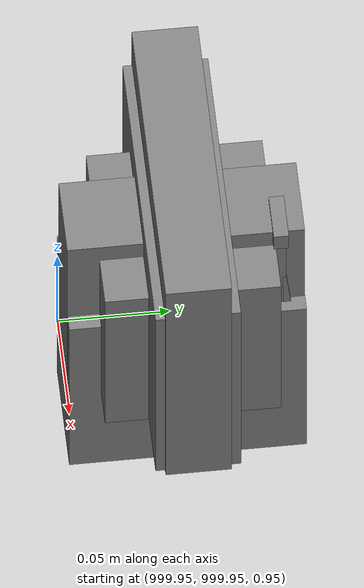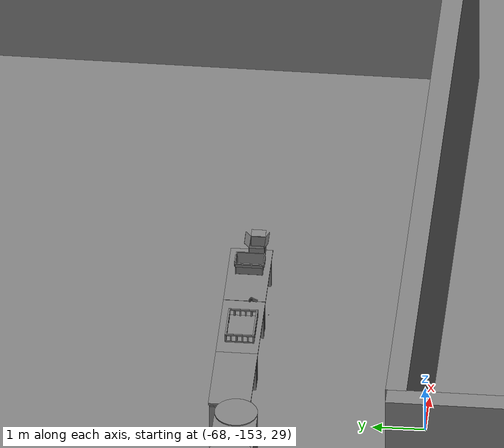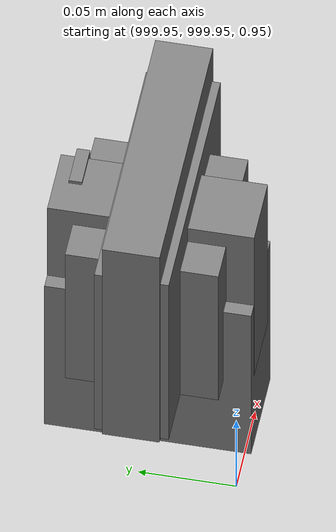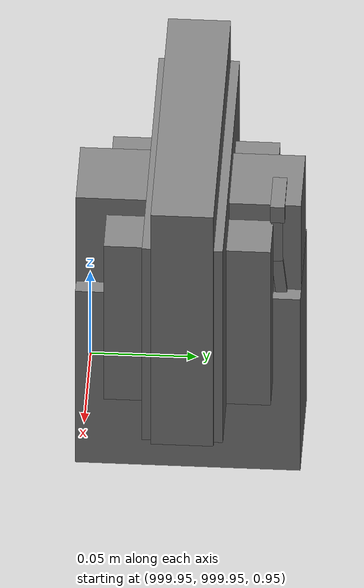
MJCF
<mujoco>
    <option gravity="0.000000000 0.000000000 -9.810000420" timestep="0.0049999999" integrator="implicitfast" density="1.225" viscosity="1.8000001e-05" noslip_iterations="10" iterations="100" sdf_iterations="50">
        <flag multiccd="disable"/>
    </option>
    <size memory="1000M"/>
    <compiler coordinate="local"/>
    <worldbody>
        <light cutoff="30" pos="0 1 1" dir="0 -1 -2"/>
        <light cutoff="30" pos="0 -1 1" dir="0 1 -2"/>
        <body pos="1000.000000000 1000.000000000 1.000000000" euler="0.000000000 0.000000000 180.000000000" name="openloong_gripper_2f85_fix_base_usda_battery_01">
            <geom contype="1" conaffinity="1" density="1000" type="box" material="" rgba="0.500000000 0.500000000 0.500000000 1.000000000" solimp="0.899999976 0.949999988 0.001000000" friction="1.000000000 0.005000000 0.000100000" solref="0.020000000 1.000000000" margin="0" condim="3" group="0" pos="-0.011123657 -0.041940309 0.101691343" quat="1.000000000 0.000000000 0.000000000 0.000000000" size="0.010800000 0.003375000 0.004725000" name="openloong_gripper_2f85_fix_base_usda_geom_4D1FABBA_48F5_49BF_8190_7C30BA77BA8D"/>
            <geom contype="1" conaffinity="1" density="1000" type="box" material="" rgba="0.500000000 0.500000000 0.500000000 1.000000000" solimp="0.899999976 0.949999988 0.001000000" friction="1.000000000 0.005000000 0.000100000" solref="0.020000000 1.000000000" margin="0" condim="3" group="0" pos="-0.010876465 -0.044247437 0.047066893" quat="0.998702705 -0.050920475 0.000000000 0.000000000" size="0.009450001 0.002700000 0.024975000" name="openloong_gripper_2f85_fix_base_usda_geom_578E6467_0263_466C_A92D_5E89F79D93C7"/>
            <geom contype="1" conaffinity="1" density="1000" type="box" material="" rgba="0.500000000 0.500000000 0.500000000 1.000000000" solimp="0.899999976 0.949999988 0.001000000" friction="1.000000000 0.005000000 0.000100000" solref="0.020000000 1.000000000" margin="0" condim="3" group="0" pos="-0.001235962 -0.000659180 0.047381196" quat="1.000000000 0.000000000 0.000000000 0.000000000" size="0.039420001 0.039150000 0.047250003" name="openloong_gripper_2f85_fix_base_usda_geom_58B576BF_9EF0_4AF6_AF51_E02DBD58AE5F"/>
            <geom contype="1" conaffinity="1" density="1000" type="box" material="" rgba="0.500000000 0.500000000 0.500000000 1.000000000" solimp="0.899999976 0.949999988 0.001000000" friction="1.000000000 0.005000000 0.000100000" solref="0.020000000 1.000000000" margin="0" condim="3" group="0" pos="-0.010876465 -0.039138794 0.009851727" quat="1.000000000 0.000000000 0.000000000 0.000000000" size="0.009450001 0.010800000 0.013500000" name="openloong_gripper_2f85_fix_base_usda_geom_7ED6A3B2_D682_48B4_B0BC_05C2983D93A8"/>
            <geom contype="1" conaffinity="1" density="1000" type="box" material="" rgba="0.500000000 0.500000000 0.500000000 1.000000000" solimp="0.899999976 0.949999988 0.001000000" friction="1.000000000 0.005000000 0.000100000" solref="0.020000000 1.000000000" margin="0" condim="3" group="0" pos="-0.010876465 -0.041528322 0.071508206" quat="1.000000000 0.000000000 0.000000000 0.000000000" size="0.009450001 0.002700000 0.027000001" name="openloong_gripper_2f85_fix_base_usda_geom_57741F0B_1177_4563_A653_F84B8542FBB1"/>
            <freejoint name="openloong_gripper_2f85_fix_base_usda_battery_01_joint"/>
            <site size="0.005000000 0.005000000 0.005000000" rgba="0.500000000 0.500000000 0.500000000 1.000000000" pos="0.000000000 0.000000000 0.000000000" quat="0.999961913 0.008726500 0.000000000 0.000000000" group="0" type="sphere" name="openloong_gripper_2f85_fix_base_usda_battery_01site"/>
        </body>
        <body pos="-66.172782898 -149.105987549 31.164155960" euler="33.325611115 71.332092285 94.083976746" mocap="true" name="spotlight3_SpotLight"/>
        <body pos="-66.373794556 -149.673660278 31.170839310" euler="-35.835128784 -47.115558624 -166.041641235" mocap="true" name="spotlight4_SpotLight"/>
        <body pos="1000.000000000 1000.000000000 1.000000000" euler="0.000000000 0.000000000 180.000000000" name="openloong_gripper_2f85_fix_base_usda_cpu_fan">
            <geom contype="1" conaffinity="1" density="1000" type="box" material="" rgba="0.500000000 0.500000000 0.500000000 1.000000000" solimp="0.899999976 0.949999988 0.001000000" friction="1.000000000 0.005000000 0.000100000" solref="0.020000000 1.000000000" margin="0" condim="3" group="0" pos="0.000000000 0.000000000 0.070034981" quat="0.000000000 0.000000000 0.000000000 1.000000000" size="0.070700005 0.014699999 0.070700005" name="openloong_gripper_2f85_fix_base_usda_geom_0DFF8B34_8B1F_44CE_BEFD_F6A13CD8A6C4"/>
            <freejoint name="openloong_gripper_2f85_fix_base_usda_cpu_fan_joint"/>
            <site size="0.005000000 0.005000000 0.005000000" rgba="0.500000000 0.500000000 0.500000000 1.000000000" pos="0.000000000 0.000000000 0.000000000" quat="0.999961913 0.008726535 0.000000000 0.000000000" group="0" type="sphere" name="openloong_gripper_2f85_fix_base_usda_cpu_fancsite"/>
        </body>
        <body pos="1000.000000000 1000.000000000 1.000000000" euler="0.000000000 0.000000000 180.000000000" name="openloong_gripper_2f85_fix_base_usda_wifi_box">
            <geom contype="1" conaffinity="1" density="1000" type="box" material="" rgba="0.500000000 0.500000000 0.500000000 1.000000000" solimp="0.899999976 0.949999988 0.001000000" friction="1.000000000 0.005000000 0.000100000" solref="0.020000000 1.000000000" margin="0" condim="3" group="0" pos="0.000000000 0.000000000 0.058978677" quat="0.000000000 0.000000047 0.000000000 1.000000000" size="0.068499997 0.018999999 0.059000000" name="openloong_gripper_2f85_fix_base_usda_geom_34539D8B_9670_4F35_A242_1BF5E6F02C3F"/>
            <freejoint name="openloong_gripper_2f85_fix_base_usda_wifi_box_joint"/>
            <site size="0.005000000 0.005000000 0.005000000" rgba="0.500000000 0.500000000 0.500000000 1.000000000" pos="0.000000000 0.000000000 0.000000000" quat="0.999961913 0.008726500 0.000000000 0.000000000" group="0" type="sphere" name="openloong_gripper_2f85_fix_base_usda_wifi_boxsite"/>
        </body>
        <body pos="-65.940093994 -149.651016235 31.167062759" euler="73.766273499 34.920543671 13.556649208" mocap="true" name="spotlight1_SpotLight"/>
        <body pos="1000.000000000 999.999938965 1.000000000" euler="0.000000000 0.000000000 180.000000000" name="openloong_gripper_2f85_fix_base_usda_intelcore_i5">
            <geom contype="1" conaffinity="1" density="1000" type="box" material="" rgba="0.500000000 0.500000000 0.500000000 1.000000000" solimp="0.899999976 0.949999988 0.001000000" friction="1.000000000 0.005000000 0.000100000" solref="0.020000000 1.000000000" margin="0" condim="3" group="0" pos="0.000000000 0.000000000 0.051722717" quat="0.707106709 0.000000000 0.000000000 -0.707106769" size="0.052800000 0.018080002 0.052800000" name="openloong_gripper_2f85_fix_base_usda_geom_3CC56212_C17A_4E3E_B0C9_1B49F3184C39"/>
            <freejoint name="openloong_gripper_2f85_fix_base_usda_intelcore_i5_joint"/>
            <site size="0.005000000 0.005000000 0.005000000" rgba="0.500000000 0.500000000 0.500000000 1.000000000" pos="0.000000000 0.000000000 0.000000000" quat="0.999961913 0.008726534 0.000000000 0.000000000" group="0" type="sphere" name="openloong_gripper_2f85_fix_base_usda_intelcore_i5site"/>
        </body>
        <body pos="1000.000000000 1000.000000000 1.000000000" euler="0.000011953 0.000005123 -179.999984741" name="openloong_gripper_2f85_fix_base_usda_intel_box">
            <geom contype="1" conaffinity="1" density="1000" type="box" material="" rgba="0.500000000 0.500000000 0.500000000 1.000000000" solimp="0.899999976 0.949999988 0.001000000" friction="1.000000000 0.005000000 0.000100000" solref="0.020000000 1.000000000" margin="0" condim="3" group="0" pos="0.000000000 -0.000067139 0.000082284" quat="0.707106709 0.000000225 0.000000253 0.707106650" size="0.052800003 0.025300000 0.052800003" name="openloong_gripper_2f85_fix_base_usda_geom_A8C9BAAB_58F2_4795_8BDD_EB3A62180B47"/>
            <freejoint name="openloong_gripper_2f85_fix_base_usda_intel_box_joint"/>
            <site size="0.005000000 0.005000000 0.005000000" rgba="0.500000000 0.500000000 0.500000000 1.000000000" pos="0.000000000 0.000000000 0.000000000" quat="0.999961913 0.008726500 0.000000000 0.000000000" group="0" type="sphere" name="openloong_gripper_2f85_fix_base_usda_intel_boxsite"/>
        </body>
        <body pos="-64.866622925 -149.383972168 30.183746338" euler="89.999984741 89.999946594 0.000000000" name="openloong_gripper_2f85_fix_base_usda_bluebox_01">
            <geom contype="1" conaffinity="1" density="1000" type="box" material="" rgba="0.500000000 0.500000000 0.500000000 1.000000000" solimp="0.899999976 0.949999988 0.001000000" friction="1.000000000 0.005000000 0.000100000" solref="0.020000000 1.000000000" margin="0" condim="3" group="0" pos="0.276580811 0.187225342 0.000068665" quat="0.707106948 0.000077471 0.707106352 0.000077486" size="0.100000001 0.057999998 0.010000000" name="openloong_gripper_2f85_fix_base_usda_geom_15089E95_B988_4BA9_BB6B_0BFB4C734A6A"/>
            <geom contype="1" conaffinity="1" density="1000" type="box" material="" rgba="0.500000000 0.500000000 0.500000000 1.000000000" solimp="0.899999976 0.949999988 0.001000000" friction="1.000000000 0.005000000 0.000100000" solref="0.020000000 1.000000000" margin="0" condim="3" group="0" pos="0.000000000 0.002883911 0.000000000" quat="0.999999881 0.000000000 0.000000000 0.000000000" size="0.254000008 0.003000000 0.172000006" name="openloong_gripper_2f85_fix_base_usda_geom_FFFA6D0A_C6F5_4529_9E9C_A724DEBF3639"/>
            <geom contype="1" conaffinity="1" density="1000" type="box" material="" rgba="0.500000000 0.500000000 0.500000000 1.000000000" solimp="0.899999976 0.949999988 0.001000000" friction="1.000000000 0.005000000 0.000100000" solref="0.020000000 1.000000000" margin="0" condim="3" group="0" pos="0.000000000 0.124874115 0.173484802" quat="0.999796331 0.020176515 -0.000000015 0.000000030" size="0.259999990 0.119999997 0.007000000" name="openloong_gripper_2f85_fix_base_usda_geom_C053E62B_0783_45F7_AB19_9D181CDDAE03"/>
            <geom contype="1" conaffinity="1" density="1000" type="box" material="" rgba="0.500000000 0.500000000 0.500000000 1.000000000" solimp="0.899999976 0.949999988 0.001000000" friction="1.000000000 0.005000000 0.000100000" solref="0.020000000 1.000000000" margin="0" condim="3" group="0" pos="0.000000000 0.124874115 -0.173469543" quat="0.999796331 -0.020176545 -0.000000015 0.000000000" size="0.259999990 0.119999997 0.007000000" name="openloong_gripper_2f85_fix_base_usda_geom_112AA673_9DB4_4FB5_A6F7_7FC7DC92EFB4"/>
            <geom contype="1" conaffinity="1" density="1000" type="box" material="" rgba="0.500000000 0.500000000 0.500000000 1.000000000" solimp="0.899999976 0.949999988 0.001000000" friction="1.000000000 0.005000000 0.000100000" solref="0.020000000 1.000000000" margin="0" condim="3" group="0" pos="0.000000000 0.214008331 0.188980103" quat="0.999912977 0.013176724 0.000000015 0.000000000" size="0.259999990 0.029999999 0.012500000" name="openloong_gripper_2f85_fix_base_usda_geom_D76452EC_E261_45CA_9491_E9F6B20094D9"/>
            <geom contype="1" conaffinity="1" density="1000" type="box" material="" rgba="0.500000000 0.500000000 0.500000000 1.000000000" solimp="0.899999976 0.949999988 0.001000000" friction="1.000000000 0.005000000 0.000100000" solref="0.020000000 1.000000000" margin="0" condim="3" group="0" pos="-0.258361816 0.125289917 0.001876831" quat="0.702796936 -0.020792112 0.710783124 0.020769298" size="0.189999998 0.119999997 0.009000000" name="openloong_gripper_2f85_fix_base_usda_geom_EFA104EA_86D3_4CFE_A1CE_18DBA3A22078"/>
            <geom contype="1" conaffinity="1" density="1000" type="box" material="" rgba="0.500000000 0.500000000 0.500000000 1.000000000" solimp="0.899999976 0.949999988 0.001000000" friction="1.000000000 0.005000000 0.000100000" solref="0.020000000 1.000000000" margin="0" condim="3" group="0" pos="0.000000000 0.214008331 -0.188980103" quat="0.999912977 -0.013176769 0.000000030 0.000000015" size="0.259999990 0.029999999 0.012500000" name="openloong_gripper_2f85_fix_base_usda_geom_6D7E9DF2_E6A1_4022_854B_CCC677626E8F"/>
            <geom contype="1" conaffinity="1" density="1000" type="box" material="" rgba="0.500000000 0.500000000 0.500000000 1.000000000" solimp="0.899999976 0.949999988 0.001000000" friction="1.000000000 0.005000000 0.000100000" solref="0.020000000 1.000000000" margin="0" condim="3" group="0" pos="-0.276611328 0.187225342 0.000068665" quat="0.707106650 0.000077441 0.707106709 0.000077456" size="0.100000001 0.057999998 0.010000000" name="openloong_gripper_2f85_fix_base_usda_geom_54715097_12D1_4F26_A837_8A7500C4D7DB"/>
            <geom contype="1" conaffinity="1" density="1000" type="box" material="" rgba="0.500000000 0.500000000 0.500000000 1.000000000" solimp="0.899999976 0.949999988 0.001000000" friction="1.000000000 0.005000000 0.000100000" solref="0.020000000 1.000000000" margin="0" condim="3" group="0" pos="0.258331299 0.125289917 0.001876831" quat="0.702851415 0.018856421 0.710823774 -0.019329369" size="0.189999998 0.119999997 0.009000000" name="openloong_gripper_2f85_fix_base_usda_geom_D4B69F09_ECA6_476C_B549_27B5C851CED5"/>
            <freejoint name="openloong_gripper_2f85_fix_base_usda_bluebox_01_joint"/>
            <site size="0.005000000 0.005000000 0.005000000" rgba="0.500000000 0.500000000 0.500000000 1.000000000" pos="0.000000000 0.000000000 0.000000000" quat="0.999961913 0.008726534 0.000000000 0.000000000" group="0" type="sphere" name="openloong_gripper_2f85_fix_base_usda_bluebox_01site"/>
        </body>
        <body pos="-64.496299744 -149.491867065 30.235729218" euler="0.000000000 0.000000000 89.999946594" name="openloong_gripper_2f85_fix_base_usda_cardboardbox_01">
            <geom contype="1" conaffinity="1" density="1000" type="box" material="" rgba="0.500000000 0.500000000 0.500000000 1.000000000" solimp="0.899999976 0.949999988 0.001000000" friction="1.000000000 0.005000000 0.000100000" solref="0.020000000 1.000000000" margin="0" condim="3" group="0" pos="-0.003166199 -0.004086494 0.005052090" quat="1.000000000 0.000000000 0.000000000 0.000000000" size="0.142499998 0.177500010 0.005000000" name="openloong_gripper_2f85_fix_base_usda_geom_1BFBD80F_08DD_4FC8_9FC4_3127F5D76278"/>
            <geom contype="1" conaffinity="1" density="1000" type="box" material="" rgba="0.500000000 0.500000000 0.500000000 1.000000000" solimp="0.899999976 0.949999988 0.001000000" friction="1.000000000 0.005000000 0.000100000" solref="0.020000000 1.000000000" margin="0" condim="3" group="0" pos="-0.003166199 0.170316696 0.150570869" quat="1.000000000 0.000000000 0.000000000 0.000000000" size="0.142499998 0.005000000 0.149999991" name="openloong_gripper_2f85_fix_base_usda_geom_F0758FB8_BA58_43C2_A522_8462E96E6ED1"/>
            <geom contype="1" conaffinity="1" density="1000" type="box" material="" rgba="0.500000000 0.500000000 0.500000000 1.000000000" solimp="0.899999976 0.949999988 0.001000000" friction="1.000000000 0.005000000 0.000100000" solref="0.020000000 1.000000000" margin="0" condim="3" group="0" pos="-0.147399902 -0.005307198 0.150570869" quat="1.000000000 0.000000000 0.000000000 0.000000000" size="0.005000000 0.177500010 0.149999991" name="openloong_gripper_2f85_fix_base_usda_geom_DF5825F4_A3E0_4D0E_86A9_0E9F41F40D32"/>
            <geom contype="1" conaffinity="1" density="1000" type="box" material="" rgba="0.500000000 0.500000000 0.500000000 1.000000000" solimp="0.899999976 0.949999988 0.001000000" friction="1.000000000 0.005000000 0.000100000" solref="0.020000000 1.000000000" margin="0" condim="3" group="0" pos="0.140275955 -0.005307198 0.150570869" quat="1.000000000 0.000000000 0.000000000 0.000000000" size="0.005000000 0.177500010 0.149999991" name="openloong_gripper_2f85_fix_base_usda_geom_A56A2E42_3F92_4803_92CA_046DE6766063"/>
            <geom contype="1" conaffinity="1" density="1000" type="box" material="" rgba="0.500000000 0.500000000 0.500000000 1.000000000" solimp="0.899999976 0.949999988 0.001000000" friction="1.000000000 0.005000000 0.000100000" solref="0.020000000 1.000000000" margin="0" condim="3" group="0" pos="-0.003166199 -0.181550980 0.150570869" quat="1.000000000 0.000000000 0.000000000 0.000000000" size="0.142499998 0.005000000 0.149999991" name="openloong_gripper_2f85_fix_base_usda_geom_A31BC229_8D8C_4616_BBBF_16CFD7A9BDDA"/>
            <freejoint name="openloong_gripper_2f85_fix_base_usda_cardboardbox_01_joint"/>
            <site size="0.005000000 0.005000000 0.005000000" rgba="0.500000000 0.500000000 0.500000000 1.000000000" pos="0.000000000 0.000000000 0.000000000" quat="0.999961913 0.008726535 0.000000000 0.000000000" group="0" type="sphere" name="openloong_gripper_2f85_fix_base_usda_site_65430C70_D107_4BB6_8BD5_E45699C8790C"/>
            <body pos="0.139160156 -0.004048347 0.301930904" euler="-179.999954224 49.383502960 179.999954224" name="openloong_gripper_2f85_fix_base_usda_A1_006">
                <geom contype="1" conaffinity="1" density="1000" type="box" material="" rgba="0.500000000 0.500000000 0.500000000 1.000000000" solimp="0.899999976 0.949999988 0.001000000" friction="1.000000000 0.005000000 0.000100000" solref="0.020000000 1.000000000" margin="0" condim="3" group="0" pos="-0.071587563 0.000009537 0.001745224" quat="0.999999881 0.000000000 0.000000000 0.000000000" size="0.071249999 0.179999992 0.002500000" name="openloong_gripper_2f85_fix_base_usda_geom_C37B2213_882E_4001_BAC1_C92853E3A996"/>
                <joint armature="0" stiffness="0.07" damping="0.0099999998" axis="0.000000 1.000000 0.000000" type="hinge" name="openloong_gripper_2f85_fix_base_usda_A1_006"/>
            </body>
            <body pos="-0.145902634 -0.004086494 0.301938057" euler="-180.000000000 -60.000011444 -180.000000000" name="openloong_gripper_2f85_fix_base_usda_A2_006">
                <geom contype="1" conaffinity="1" density="1000" type="box" material="" rgba="0.500000000 0.500000000 0.500000000 1.000000000" solimp="0.899999976 0.949999988 0.001000000" friction="1.000000000 0.005000000 0.000100000" solref="0.020000000 1.000000000" margin="0" condim="3" group="0" pos="0.071268082 0.000009537 0.002717972" quat="0.000002921 0.000000000 -0.000000030 0.999999881" size="0.071249999 0.179999992 0.002500000" name="openloong_gripper_2f85_fix_base_usda_geom_73F5E5CA_CF30_45CE_997B_41A4F0774FE9"/>
                <joint armature="0" stiffness="0.07" damping="0.0099999998" axis="0.000000 1.000000 0.000000" type="hinge" name="openloong_gripper_2f85_fix_base_usda_A2_006"/>
            </body>
            <body pos="-0.003385544 0.175991058 0.301930904" euler="-125.858116150 -0.000004561 0.000002331" name="openloong_gripper_2f85_fix_base_usda_B2_006">
                <geom contype="1" conaffinity="1" density="1000" type="box" material="" rgba="0.500000000 0.500000000 0.500000000 1.000000000" solimp="0.899999976 0.949999988 0.001000000" friction="1.000000000 0.005000000 0.000100000" solref="0.020000000 1.000000000" margin="0" condim="3" group="0" pos="0.000009537 -0.070939064 -0.002470016" quat="0.999614120 0.027776197 -0.000000015 0.000000030" size="0.137500003 0.064999998 0.005000000" name="openloong_gripper_2f85_fix_base_usda_geom_98364739_4960_4FEF_806C_03233DE5BA98"/>
                <joint armature="0" stiffness="0.07" damping="0.0099999998" axis="1.000000 0.000000 0.000000" type="hinge" name="openloong_gripper_2f85_fix_base_usda_B2_006"/>
            </body>
            <body pos="-0.003385544 -0.184140205 0.301938057" euler="147.805557251 0.000000000 0.000000000" name="openloong_gripper_2f85_fix_base_usda_B1_006">
                <geom contype="1" conaffinity="1" density="1000" type="box" material="" rgba="0.500000000 0.500000000 0.500000000 1.000000000" solimp="0.899999976 0.949999988 0.001000000" friction="1.000000000 0.005000000 0.000100000" solref="0.020000000 1.000000000" margin="0" condim="3" group="0" pos="-0.000028610 0.070202351 -0.002703667" quat="0.999614179 -0.027776167 0.000000000 0.000000000" size="0.137500003 0.064999998 0.005000000" name="openloong_gripper_2f85_fix_base_usda_geom_43498F86_1AC0_4C04_B651_1675338FD7D5"/>
                <joint armature="0" stiffness="0.07" damping="0.0099999998" axis="1.000000 0.000000 0.000000" type="hinge" name="openloong_gripper_2f85_fix_base_usda_B1_006"/>
            </body>
        </body>
        <body pos="-65.882858276 -149.481979370 30.229999542" euler="-64.487716675 0.000000000 0.000000000" name="openloong_gripper_2f85_fix_base_usda_Barcode">
            <geom contype="1" conaffinity="1" density="1000" type="box" material="" rgba="0.500000000 0.500000000 0.500000000 1.000000000" solimp="0.899999976 0.949999988 0.001000000" friction="1.000000000 0.005000000 0.000100000" solref="0.020000000 1.000000000" margin="0" condim="3" group="0" pos="0.000000000 0.013038635 0.001419067" quat="0.000000000 0.000000000 0.000000000 1.000000119" size="0.034000002 0.010000000 0.017999999" name="openloong_gripper_2f85_fix_base_usda_geom_9D8E2544_6DA5_4CAE_B956_F9E64E62EC60"/>
            <geom contype="1" conaffinity="1" density="1000" type="box" material="" rgba="0.500000000 0.500000000 0.500000000 1.000000000" solimp="0.899999976 0.949999988 0.001000000" friction="1.000000000 0.005000000 0.000100000" solref="0.020000000 1.000000000" margin="0" condim="3" group="0" pos="0.000000000 -0.035301208 -0.007095337" quat="0.000000000 0.000000000 -0.043619365 0.999048233" size="0.028999999 0.010000000 0.020000000" name="openloong_gripper_2f85_fix_base_usda_geom_911A25E4_576C_4940_B17E_9F5A650D647B"/>
            <geom contype="1" conaffinity="1" density="1000" type="box" material="" rgba="0.500000000 0.500000000 0.500000000 1.000000000" solimp="0.899999976 0.949999988 0.001000000" friction="1.000000000 0.005000000 0.000100000" solref="0.020000000 1.000000000" margin="0" condim="3" group="0" pos="0.000000000 -0.043411255 -0.011749268" quat="0.922262907 0.386563420 0.000000000 0.000000000" size="0.026000001 0.010000000 0.020000000" name="openloong_gripper_2f85_fix_base_usda_geom_091802D8_2F52_4042_A737_A0C890CAD463"/>
            <geom contype="1" conaffinity="1" density="1000" type="box" material="" rgba="0.500000000 0.500000000 0.500000000 1.000000000" solimp="0.899999976 0.949999988 0.001000000" friction="1.000000000 0.005000000 0.000100000" solref="0.020000000 1.000000000" margin="0" condim="3" group="0" pos="0.000000000 -0.016967773 -0.031860352" quat="0.000000000 0.000000000 0.000000000 1.000000119" size="0.008000000 0.010000000 0.013000000" name="openloong_gripper_2f85_fix_base_usda_geom_3CF01799_6178_4CD8_9D8C_B3E9F0CADC77"/>
            <geom contype="1" conaffinity="1" density="1000" type="box" material="" rgba="0.500000000 0.500000000 0.500000000 1.000000000" solimp="0.899999976 0.949999988 0.001000000" friction="1.000000000 0.005000000 0.000100000" solref="0.020000000 1.000000000" margin="0" condim="3" group="0" pos="0.000000000 -0.001869202 0.000312805" quat="0.953716993 0.300705761 0.000000000 0.000000000" size="0.032000002 0.010000000 0.018999999" name="openloong_gripper_2f85_fix_base_usda_geom_20326E08_F83D_4319_AC20_5BCE5027DBEB"/>
            <geom contype="1" conaffinity="1" density="1000" type="box" material="" rgba="0.500000000 0.500000000 0.500000000 1.000000000" solimp="0.899999976 0.949999988 0.001000000" friction="1.000000000 0.005000000 0.000100000" solref="0.020000000 1.000000000" margin="0" condim="3" group="0" pos="0.000000000 -0.019531250 -0.003173828" quat="0.953716993 0.300705761 0.000000000 0.000000000" size="0.030999999 0.010000000 0.020000000" name="openloong_gripper_2f85_fix_base_usda_geom_75B43A8A_41E0_4C62_8917_61A49534C4DD"/>
            <geom contype="1" conaffinity="1" density="1000" type="box" material="" rgba="0.500000000 0.500000000 0.500000000 1.000000000" solimp="0.899999976 0.949999988 0.001000000" friction="1.000000000 0.005000000 0.000100000" solref="0.020000000 1.000000000" margin="0" condim="3" group="0" pos="0.000000000 -0.035301208 -0.007095337" quat="0.953716993 0.300705761 0.000000000 0.000000000" size="0.028999999 0.010000000 0.020000000" name="openloong_gripper_2f85_fix_base_usda_geom_E0A64C0E_8FC9_4722_A0E5_AEFA0EB03CE9"/>
            <geom contype="1" conaffinity="1" density="1000" type="box" material="" rgba="0.500000000 0.500000000 0.500000000 1.000000000" solimp="0.899999976 0.949999988 0.001000000" friction="1.000000000 0.005000000 0.000100000" solref="0.020000000 1.000000000" margin="0" condim="3" group="0" pos="0.000000000 -0.042617798 -0.071121216" quat="0.000000000 0.000000000 0.000000000 1.000000119" size="0.013000000 0.021000000 0.059999999" name="openloong_gripper_2f85_fix_base_usda_geom_0803E390_A177_41EA_9485_674710D770CA"/>
            <freejoint name="openloong_gripper_2f85_fix_base_usda_Barcode_joint"/>
            <site size="0.005000000 0.005000000 0.005000000" rgba="0.500000000 0.500000000 0.500000000 1.000000000" pos="0.000000000 0.000000000 0.000000000" quat="1.000000000 0.000000000 0.000000000 0.000000000" group="0" type="sphere" name="openloong_gripper_2f85_fix_base_usda_Barcode_site"/>
        </body>
        <body pos="-66.745018005 -149.392349243 30.184000015" euler="0.000000000 0.000000000 89.999946594" name="[22331480462297]_Basket_01">
            <geom contype="1" conaffinity="1" density="1000" type="box" material="" rgba="0.500000000 0.500000000 0.500000000 1.000000000" solimp="0.899999976 0.949999988 0.001000000" friction="1.000000000 0.005000000 0.000100000" solref="0.020000000 1.000000000" margin="0" condim="3" group="0" pos="-0.052425385 0.389207840 0.089787483" quat="0.707107008 0.000000000 0.000000000 0.707106411" size="0.014249999 0.014249999 0.059999999" name="[22331480462297]_geom_34CC7DCF_F070_46ED_B762_1C0F3D8969DA"/>
            <geom contype="1" conaffinity="1" density="1000" type="box" material="" rgba="0.500000000 0.500000000 0.500000000 1.000000000" solimp="0.899999976 0.949999988 0.001000000" friction="1.000000000 0.005000000 0.000100000" solref="0.020000000 1.000000000" margin="0" condim="3" group="0" pos="0.264015198 -0.133043289 0.089787483" quat="0.707107008 0.000000000 0.000000000 0.707106411" size="0.014249999 0.014249999 0.059999999" name="[22331480462297]_geom_476BF396_30C5_4F9C_9CD0_0C8761D96280"/>
            <geom contype="1" conaffinity="1" density="1000" type="box" material="" rgba="0.500000000 0.500000000 0.500000000 1.000000000" solimp="0.899999976 0.949999988 0.001000000" friction="1.000000000 0.005000000 0.000100000" solref="0.020000000 1.000000000" margin="0" condim="3" group="0" pos="-0.264015198 -0.265548706 0.089793205" quat="0.707107008 0.000000000 0.000000000 0.707106411" size="0.014249999 0.014249999 0.059999999" name="[22331480462297]_geom_55CB3382_DE05_4BEC_A8FC_65A1B16BBF49"/>
            <geom contype="1" conaffinity="1" density="1000" type="box" material="" rgba="0.500000000 0.500000000 0.500000000 1.000000000" solimp="0.899999976 0.949999988 0.001000000" friction="1.000000000 0.005000000 0.000100000" solref="0.020000000 1.000000000" margin="0" condim="3" group="0" pos="-0.160263062 -0.389322281 0.089793205" quat="0.707107008 0.000000000 0.000000000 0.707106411" size="0.014249999 0.014249999 0.059999999" name="[22331480462297]_geom_5641B1E2_7870_4CCB_8C1F_C012FAEFC192"/>
            <geom contype="1" conaffinity="1" density="1000" type="box" material="" rgba="0.500000000 0.500000000 0.500000000 1.000000000" solimp="0.899999976 0.949999988 0.001000000" friction="1.000000000 0.005000000 0.000100000" solref="0.020000000 1.000000000" margin="0" condim="3" group="0" pos="0.162265778 -0.389322281 0.089787483" quat="0.707107008 0.000000000 0.000000000 0.707106411" size="0.014249999 0.014249999 0.059999999" name="[22331480462297]_geom_2FE50D29_04CB_4B4B_A8AB_EDC9AB599A05"/>
            <geom contype="1" conaffinity="1" density="1000" type="box" material="" rgba="0.500000000 0.500000000 0.500000000 1.000000000" solimp="0.899999976 0.949999988 0.001000000" friction="1.000000000 0.005000000 0.000100000" solref="0.020000000 1.000000000" margin="0" condim="3" group="0" pos="0.264015198 0.389207840 0.089787483" quat="0.707107008 0.000000000 0.000000000 0.707106411" size="0.014249999 0.014249999 0.059999999" name="[22331480462297]_geom_9EA568E1_3947_4AB3_8C79_15CBFBF77745"/>
            <geom contype="1" conaffinity="1" density="1000" type="box" material="" rgba="0.500000000 0.500000000 0.500000000 1.000000000" solimp="0.899999976 0.949999988 0.001000000" friction="1.000000000 0.005000000 0.000100000" solref="0.020000000 1.000000000" margin="0" condim="3" group="0" pos="-0.264015198 -0.133043289 0.089793205" quat="0.707107008 0.000000000 0.000000000 0.707106411" size="0.014249999 0.014249999 0.059999999" name="[22331480462297]_geom_9B4F99A6_AA3F_4CEE_954C_CB290BBD888F"/>
            <geom contype="1" conaffinity="1" density="1000" type="box" material="" rgba="0.500000000 0.500000000 0.500000000 1.000000000" solimp="0.899999976 0.949999988 0.001000000" friction="1.000000000 0.005000000 0.000100000" solref="0.020000000 1.000000000" margin="0" condim="3" group="0" pos="-0.264026642 0.269256592 0.089793205" quat="0.707107008 0.000000000 0.000000000 0.707106411" size="0.014249999 0.014249999 0.059999999" name="[22331480462297]_geom_ACF07BC9_86A8_4093_B709_088F38B327BC"/>
            <geom contype="1" conaffinity="1" density="1000" type="box" material="" rgba="0.500000000 0.500000000 0.500000000 1.000000000" solimp="0.899999976 0.949999988 0.001000000" friction="1.000000000 0.005000000 0.000100000" solref="0.020000000 1.000000000" margin="0" condim="3" group="0" pos="0.054462433 0.389207840 0.089787483" quat="0.707107008 0.000000000 0.000000000 0.707106411" size="0.014249999 0.014249999 0.059999999" name="[22331480462297]_geom_35F99165_2033_4625_8FBC_FA4F95E50059"/>
            <geom contype="1" conaffinity="1" density="1000" type="box" material="" rgba="0.500000000 0.500000000 0.500000000 1.000000000" solimp="0.899999976 0.949999988 0.001000000" friction="1.000000000 0.005000000 0.000100000" solref="0.020000000 1.000000000" margin="0" condim="3" group="0" pos="0.054462433 -0.389322281 0.089787483" quat="0.707107008 0.000000000 0.000000000 0.707106411" size="0.014249999 0.014249999 0.059999999" name="[22331480462297]_geom_6DED188E_8799_4804_B24D_4BA3B93EBA4F"/>
            <geom contype="1" conaffinity="1" density="1000" type="box" material="" rgba="0.500000000 0.500000000 0.500000000 1.000000000" solimp="0.899999976 0.949999988 0.001000000" friction="1.000000000 0.005000000 0.000100000" solref="0.020000000 1.000000000" margin="0" condim="3" group="0" pos="0.264015198 0.269256592 0.089793205" quat="0.707107008 0.000000000 0.000000000 0.707106411" size="0.014249999 0.014249999 0.059999999" name="[22331480462297]_geom_B164DDD7_2404_4056_96C7_F20D47E1372C"/>
            <geom contype="1" conaffinity="1" density="1000" type="box" material="" rgba="0.500000000 0.500000000 0.500000000 1.000000000" solimp="0.899999976 0.949999988 0.001000000" friction="1.000000000 0.005000000 0.000100000" solref="0.020000000 1.000000000" margin="0" condim="3" group="0" pos="0.264015198 -0.389322281 0.089787483" quat="0.707107008 0.000000000 0.000000000 0.707106411" size="0.014249999 0.014249999 0.059999999" name="[22331480462297]_geom_D291CE19_0AE4_4301_B853_5EA01E6D29EC"/>
            <geom contype="1" conaffinity="1" density="1000" type="box" material="" rgba="0.500000000 0.500000000 0.500000000 1.000000000" solimp="0.899999976 0.949999988 0.001000000" friction="1.000000000 0.005000000 0.000100000" solref="0.020000000 1.000000000" margin="0" condim="3" group="0" pos="0.000000000 0.000000000 0.015998840" quat="0.707107008 0.000000000 0.000000000 0.707106411" size="0.403499991 0.279000014 0.015750000" name="[22331480462297]_geom_0601A8CA_09C1_423A_B408_BCA712E0F730"/>
            <geom contype="1" conaffinity="1" density="1000" type="box" material="" rgba="0.500000000 0.500000000 0.500000000 1.000000000" solimp="0.899999976 0.949999988 0.001000000" friction="1.000000000 0.005000000 0.000100000" solref="0.020000000 1.000000000" margin="0" condim="3" group="0" pos="0.000000000 -0.389476776 0.163619041" quat="0.707107008 0.000000000 0.000000000 0.707106411" size="0.015000000 0.277500004 0.015750000" name="[22331480462297]_geom_FEA4A4FE_FD6C_49AD_A7CF_B495C5B41B2C"/>
            <geom contype="1" conaffinity="1" density="1000" type="box" material="" rgba="0.500000000 0.500000000 0.500000000 1.000000000" solimp="0.899999976 0.949999988 0.001000000" friction="1.000000000 0.005000000 0.000100000" solref="0.020000000 1.000000000" margin="0" condim="3" group="0" pos="0.162265778 0.389207840 0.089787483" quat="0.707107008 0.000000000 0.000000000 0.707106411" size="0.014249999 0.014249999 0.059999999" name="[22331480462297]_geom_4869BA2C_6C8F_4F8E_A1D2_87A4D51A644C"/>
            <geom contype="1" conaffinity="1" density="1000" type="box" material="" rgba="0.500000000 0.500000000 0.500000000 1.000000000" solimp="0.899999976 0.949999988 0.001000000" friction="1.000000000 0.005000000 0.000100000" solref="0.020000000 1.000000000" margin="0" condim="3" group="0" pos="0.000000000 0.389471054 0.163619041" quat="0.707107008 0.000000000 0.000000000 0.707106411" size="0.015000000 0.277500004 0.015750000" name="[22331480462297]_geom_FB273A5E_F32D_4647_925C_0C42457DAC9C"/>
            <geom contype="1" conaffinity="1" density="1000" type="box" material="" rgba="0.500000000 0.500000000 0.500000000 1.000000000" solimp="0.899999976 0.949999988 0.001000000" friction="1.000000000 0.005000000 0.000100000" solref="0.020000000 1.000000000" margin="0" condim="3" group="0" pos="-0.263511658 0.000000000 0.163619041" quat="0.707107008 0.000000000 0.000000000 0.707106411" size="0.403499991 0.015000000 0.015750000" name="[22331480462297]_geom_C8D9521E_42F7_45CC_B2D0_359956A98AA3"/>
            <geom contype="1" conaffinity="1" density="1000" type="box" material="" rgba="0.500000000 0.500000000 0.500000000 1.000000000" solimp="0.899999976 0.949999988 0.001000000" friction="1.000000000 0.005000000 0.000100000" solref="0.020000000 1.000000000" margin="0" condim="3" group="0" pos="-0.264015198 0.141334534 0.089793205" quat="0.707107008 0.000000000 0.000000000 0.707106411" size="0.014249999 0.014249999 0.059999999" name="[22331480462297]_geom_44E23529_2867_4484_B82F_F20FC346ADF8"/>
            <geom contype="1" conaffinity="1" density="1000" type="box" material="" rgba="0.500000000 0.500000000 0.500000000 1.000000000" solimp="0.899999976 0.949999988 0.001000000" friction="1.000000000 0.005000000 0.000100000" solref="0.020000000 1.000000000" margin="0" condim="3" group="0" pos="0.264015198 -0.265548706 0.089787483" quat="0.707107008 0.000000000 0.000000000 0.707106411" size="0.014249999 0.014249999 0.059999999" name="[22331480462297]_geom_67187D6D_B355_4C65_BC00_F4425033A0F4"/>
            <geom contype="1" conaffinity="1" density="1000" type="box" material="" rgba="0.500000000 0.500000000 0.500000000 1.000000000" solimp="0.899999976 0.949999988 0.001000000" friction="1.000000000 0.005000000 0.000100000" solref="0.020000000 1.000000000" margin="0" condim="3" group="0" pos="-0.160263062 0.389207840 0.089787483" quat="0.707107008 0.000000000 0.000000000 0.707106411" size="0.014249999 0.014249999 0.059999999" name="[22331480462297]_geom_EBBC0332_71E4_466B_A4F1_8DB27CF269A3"/>
            <geom contype="1" conaffinity="1" density="1000" type="box" material="" rgba="0.500000000 0.500000000 0.500000000 1.000000000" solimp="0.899999976 0.949999988 0.001000000" friction="1.000000000 0.005000000 0.000100000" solref="0.020000000 1.000000000" margin="0" condim="3" group="0" pos="-0.052425385 -0.389322281 0.089787483" quat="0.707107008 0.000000000 0.000000000 0.707106411" size="0.014249999 0.014249999 0.059999999" name="[22331480462297]_geom_F3F6E69B_C077_4BD8_BBFC_2F405C6EBD7A"/>
            <geom contype="1" conaffinity="1" density="1000" type="box" material="" rgba="0.500000000 0.500000000 0.500000000 1.000000000" solimp="0.899999976 0.949999988 0.001000000" friction="1.000000000 0.005000000 0.000100000" solref="0.020000000 1.000000000" margin="0" condim="3" group="0" pos="-0.264026642 -0.389322281 0.089793205" quat="0.707107008 0.000000000 0.000000000 0.707106411" size="0.014249999 0.014249999 0.059999999" name="[22331480462297]_geom_9B45AF57_CD6A_4E65_8E36_E9660BA81313"/>
            <geom contype="1" conaffinity="1" density="1000" type="box" material="" rgba="0.500000000 0.500000000 0.500000000 1.000000000" solimp="0.899999976 0.949999988 0.001000000" friction="1.000000000 0.005000000 0.000100000" solref="0.020000000 1.000000000" margin="0" condim="3" group="0" pos="0.264015198 0.141334534 0.089787483" quat="0.707107008 0.000000000 0.000000000 0.707106411" size="0.014249999 0.014249999 0.059999999" name="[22331480462297]_geom_0AB7AE55_4928_44C9_9354_C6D5DFC18D79"/>
            <geom contype="1" conaffinity="1" density="1000" type="box" material="" rgba="0.500000000 0.500000000 0.500000000 1.000000000" solimp="0.899999976 0.949999988 0.001000000" friction="1.000000000 0.005000000 0.000100000" solref="0.020000000 1.000000000" margin="0" condim="3" group="0" pos="-0.264015198 0.389207840 0.089793205" quat="0.707107008 0.000000000 0.000000000 0.707106411" size="0.014249999 0.014249999 0.059999999" name="[22331480462297]_geom_3820BD3D_5802_4B36_BB3A_7B99F40C3483"/>
            <geom contype="1" conaffinity="1" density="1000" type="box" material="" rgba="0.500000000 0.500000000 0.500000000 1.000000000" solimp="0.899999976 0.949999988 0.001000000" friction="1.000000000 0.005000000 0.000100000" solref="0.020000000 1.000000000" margin="0" condim="3" group="0" pos="0.264015198 0.004480362 0.089787483" quat="0.707107008 0.000000000 0.000000000 0.707106411" size="0.014249999 0.014249999 0.059999999" name="[22331480462297]_geom_18148A3B_3A0A_4052_8B3D_A61AB6E8E930"/>
            <geom contype="1" conaffinity="1" density="1000" type="box" material="" rgba="0.500000000 0.500000000 0.500000000 1.000000000" solimp="0.899999976 0.949999988 0.001000000" friction="1.000000000 0.005000000 0.000100000" solref="0.020000000 1.000000000" margin="0" condim="3" group="0" pos="0.263694763 -0.000011444 0.163619041" quat="0.707107008 0.000000000 0.000000000 0.707106411" size="0.403499991 0.015000000 0.015750000" name="[22331480462297]_geom_0100731C_A1B2_4B67_B5C3_E72B1950D100"/>
            <geom contype="1" conaffinity="1" density="1000" type="box" material="" rgba="0.500000000 0.500000000 0.500000000 1.000000000" solimp="0.899999976 0.949999988 0.001000000" friction="1.000000000 0.005000000 0.000100000" solref="0.020000000 1.000000000" margin="0" condim="3" group="0" pos="-0.264015198 0.004480362 0.089793205" quat="0.707107008 0.000000000 0.000000000 0.707106411" size="0.014249999 0.014249999 0.059999999" name="[22331480462297]_geom_4BCCE0FE_E454_4F89_9E83_1351525D5C05"/>
            <freejoint name="[22331480462297]_joint_7E2BA9D3_E6BB_4B6E_8601_D7486D7DD7CE"/>
        </body>
        <body pos="0.000000000 0.000000000 0.000000000" euler="0.000000000 0.000000000 0.000000000" name="Static Objects_Static Objects">
            <geom contype="1" conaffinity="1" density="1000" type="box" material="" rgba="0.500000000 0.500000000 0.500000000 1.000000000" solimp="0.899999976 0.949999988 0.001000000" friction="1.000000000 0.005000000 0.000100000" solref="0.020000000 1.000000000" margin="0" condim="3" group="0" pos="-67.544113159 -149.365814209 29.727830887" quat="0.500000417 0.499999970 0.499999553 0.499999970" size="0.381000012 0.319999993 0.041000001" name="Static Objects_geom_685ACD26_F146_4BED_801E_93CB1FCF8F6B"/>
            <geom contype="1" conaffinity="1" density="1000" type="box" material="" rgba="0.500000000 0.500000000 0.500000000 1.000000000" solimp="0.899999976 0.949999988 0.001000000" friction="1.000000000 0.005000000 0.000100000" solref="0.020000000 1.000000000" margin="0" condim="3" group="0" pos="-68.239501953 -149.365814209 30.086868286" quat="0.500000417 0.499999970 0.499999553 0.499999970" size="0.370999992 0.039500002 0.745000005" name="Static Objects_geom_65BF9C77_EE46_4D99_B486_52E5ABADA901"/>
            <geom contype="1" conaffinity="1" density="1000" type="box" material="" rgba="0.500000000 0.500000000 0.500000000 1.000000000" solimp="0.899999976 0.949999988 0.001000000" friction="1.000000000 0.005000000 0.000100000" solref="0.020000000 1.000000000" margin="0" condim="3" group="0" pos="-68.239501953 -149.365814209 30.147235870" quat="0.500000417 0.499999970 0.499999553 0.499999970" size="0.400000006 0.022000000 0.800000012" name="Static Objects_geom_D3A9FFCC_FCAF_4BCF_89DC_E81B5B363383"/>
            <geom contype="1" conaffinity="1" density="1000" type="box" material="" rgba="0.500000000 0.500000000 0.500000000 1.000000000" solimp="0.899999976 0.949999988 0.001000000" friction="1.000000000 0.005000000 0.000100000" solref="0.020000000 1.000000000" margin="0" condim="3" group="0" pos="-68.934890747 -149.365814209 29.727830887" quat="0.500000417 0.499999970 0.499999553 0.499999970" size="0.381000012 0.319999993 0.041000001" name="Static Objects_geom_D3CFAE16_1783_4BBB_A883_FF79765899C7"/>
            <geom contype="1" conaffinity="1" density="1000" type="box" material="" rgba="0.500000000 0.500000000 0.500000000 1.000000000" solimp="0.899999976 0.949999988 0.001000000" friction="1.000000000 0.005000000 0.000100000" solref="0.020000000 1.000000000" margin="0" condim="3" group="0" pos="-68.239501953 -149.365814209 29.561563492" quat="0.500000417 0.499999970 0.499999553 0.499999970" size="0.020000000 0.022000000 0.660000026" name="Static Objects_geom_A07AE4F4_8B8D_49A1_9101_14FFC1A6E88C"/>
            <geom contype="1" conaffinity="1" density="1000" type="box" material="" rgba="0.500000000 0.500000000 0.500000000 1.000000000" solimp="0.899999976 0.949999988 0.001000000" friction="1.000000000 0.005000000 0.000100000" solref="0.020000000 1.000000000" margin="0" condim="3" group="0" pos="-65.945671082 -149.365814209 29.727830887" quat="0.500000417 0.499999970 0.499999553 0.499999970" size="0.381000012 0.319999993 0.041000001" name="Static Objects_geom_404C5504_BD62_4340_85A8_F2D8268082A7"/>
            <geom contype="1" conaffinity="1" density="1000" type="box" material="" rgba="0.500000000 0.500000000 0.500000000 1.000000000" solimp="0.899999976 0.949999988 0.001000000" friction="1.000000000 0.005000000 0.000100000" solref="0.020000000 1.000000000" margin="0" condim="3" group="0" pos="-66.641059875 -149.365814209 30.086868286" quat="0.500000417 0.499999970 0.499999553 0.499999970" size="0.370999992 0.039500002 0.745000005" name="Static Objects_geom_BDC8000A_328D_457B_B63F_B176B11FB0AC"/>
            <geom contype="1" conaffinity="1" density="1000" type="box" material="" rgba="0.500000000 0.500000000 0.500000000 1.000000000" solimp="0.899999976 0.949999988 0.001000000" friction="1.000000000 0.005000000 0.000100000" solref="0.020000000 1.000000000" margin="0" condim="3" group="0" pos="-66.641059875 -149.365814209 30.147235870" quat="0.500000417 0.499999970 0.499999553 0.499999970" size="0.400000006 0.022000000 0.800000012" name="Static Objects_geom_8C508FAF_57B4_4761_B2A8_B8212732142B"/>
            <geom contype="1" conaffinity="1" density="1000" type="box" material="" rgba="0.500000000 0.500000000 0.500000000 1.000000000" solimp="0.899999976 0.949999988 0.001000000" friction="1.000000000 0.005000000 0.000100000" solref="0.020000000 1.000000000" margin="0" condim="3" group="0" pos="-67.336448669 -149.365814209 29.727830887" quat="0.500000417 0.499999970 0.499999553 0.499999970" size="0.381000012 0.319999993 0.041000001" name="Static Objects_geom_338C5765_1E6E_43E8_97B6_8F079B6A06A2"/>
            <geom contype="1" conaffinity="1" density="1000" type="box" material="" rgba="0.500000000 0.500000000 0.500000000 1.000000000" solimp="0.899999976 0.949999988 0.001000000" friction="1.000000000 0.005000000 0.000100000" solref="0.020000000 1.000000000" margin="0" condim="3" group="0" pos="-66.641059875 -149.365814209 29.561563492" quat="0.500000417 0.499999970 0.499999553 0.499999970" size="0.020000000 0.022000000 0.660000026" name="Static Objects_geom_525DB502_5BB5_443E_ABE2_FF57EA445CBA"/>
            <geom contype="1" conaffinity="1" density="1000" type="box" material="" rgba="0.500000000 0.500000000 0.500000000 1.000000000" solimp="0.899999976 0.949999988 0.001000000" friction="1.000000000 0.005000000 0.000100000" solref="0.020000000 1.000000000" margin="0" condim="3" group="0" pos="-64.338577271 -149.365814209 29.727830887" quat="0.500000417 0.499999970 0.499999553 0.499999970" size="0.381000012 0.319999993 0.041000001" name="Static Objects_geom_0DBB3C4E_6815_4DEA_9623_8C89E6A8D446"/>
            <geom contype="1" conaffinity="1" density="1000" type="box" material="" rgba="0.500000000 0.500000000 0.500000000 1.000000000" solimp="0.899999976 0.949999988 0.001000000" friction="1.000000000 0.005000000 0.000100000" solref="0.020000000 1.000000000" margin="0" condim="3" group="0" pos="-65.033966064 -149.365814209 30.086868286" quat="0.500000417 0.499999970 0.499999553 0.499999970" size="0.370999992 0.039500002 0.745000005" name="Static Objects_geom_636B6D53_9E69_47AF_A9D4_C761663D1D92"/>
            <geom contype="1" conaffinity="1" density="1000" type="box" material="" rgba="0.500000000 0.500000000 0.500000000 1.000000000" solimp="0.899999976 0.949999988 0.001000000" friction="1.000000000 0.005000000 0.000100000" solref="0.020000000 1.000000000" margin="0" condim="3" group="0" pos="-65.033966064 -149.365814209 30.147235870" quat="0.500000417 0.499999970 0.499999553 0.499999970" size="0.400000006 0.022000000 0.800000012" name="Static Objects_geom_A9010F8C_9CF4_4109_8A6B_F6622714DA4E"/>
            <geom contype="1" conaffinity="1" density="1000" type="box" material="" rgba="0.500000000 0.500000000 0.500000000 1.000000000" solimp="0.899999976 0.949999988 0.001000000" friction="1.000000000 0.005000000 0.000100000" solref="0.020000000 1.000000000" margin="0" condim="3" group="0" pos="-65.729354858 -149.365814209 29.727830887" quat="0.500000417 0.499999970 0.499999553 0.499999970" size="0.381000012 0.319999993 0.041000001" name="Static Objects_geom_57C9F176_BFB3_467F_B0F5_6515AF2634B3"/>
            <geom contype="1" conaffinity="1" density="1000" type="box" material="" rgba="0.500000000 0.500000000 0.500000000 1.000000000" solimp="0.899999976 0.949999988 0.001000000" friction="1.000000000 0.005000000 0.000100000" solref="0.020000000 1.000000000" margin="0" condim="3" group="0" pos="-65.033966064 -149.365814209 29.561563492" quat="0.500000417 0.499999970 0.499999553 0.499999970" size="0.020000000 0.022000000 0.660000026" name="Static Objects_geom_95AC685C_8D4F_44CB_A1DA_FCED52014643"/>
            <geom contype="1" conaffinity="1" density="1000" type="box" material="" rgba="0.500000000 0.500000000 0.500000000 1.000000000" solimp="0.899999976 0.949999988 0.001000000" friction="1.000000000 0.005000000 0.000100000" solref="0.020000000 1.000000000" margin="0" condim="3" group="0" pos="-61.754566193 -137.853729248 33.906845093" quat="0.707107067 0.000000000 0.000000000 0.707106471" size="0.759999990 0.759999990 4.500000000" name="Static Objects_geom_54E8D392_1D64_425D_98C3_DCE94025E455"/>
            <geom contype="1" conaffinity="1" density="1000" type="box" material="" rgba="0.500000000 0.500000000 0.500000000 1.000000000" solimp="0.899999976 0.949999988 0.001000000" friction="1.000000000 0.005000000 0.000100000" solref="0.020000000 1.000000000" margin="0" condim="3" group="0" pos="-57.511135101 -144.927108765 31.707921982" quat="1.000000000 0.000000000 0.000000000 0.000000000" size="0.200000003 8.000000000 2.299999952" name="Static Objects_geom_3A0BDD7D_E19A_41B2_9D1D_07C08B5D8B48"/>
            <geom contype="1" conaffinity="1" density="1000" type="box" material="" rgba="0.500000000 0.500000000 0.500000000 1.000000000" solimp="0.899999976 0.949999988 0.001000000" friction="1.000000000 0.005000000 0.000100000" solref="0.020000000 1.000000000" margin="0" condim="3" group="0" pos="-80.517646790 -157.574050903 31.688196182" quat="0.707107067 0.000000000 0.000000000 0.707106471" size="0.600000024 0.600000024 2.299999952" name="Static Objects_geom_DFCEC290_585B_4921_AF82_3AB13B615E24"/>
            <geom contype="1" conaffinity="1" density="1000" type="box" material="" rgba="0.500000000 0.500000000 0.500000000 1.000000000" solimp="0.899999976 0.949999988 0.001000000" friction="1.000000000 0.005000000 0.000100000" solref="0.020000000 1.000000000" margin="0" condim="3" group="0" pos="-80.711044312 -147.414932251 31.666158676" quat="1.000000000 0.000000000 0.000000000 0.000000000" size="0.200000003 10.000000000 2.299999952" name="Static Objects_geom_10478006_7BDB_46C8_9123_C155C6B2E819"/>
            <geom contype="1" conaffinity="1" density="1000" type="box" material="" rgba="0.500000000 0.500000000 0.500000000 1.000000000" solimp="0.899999976 0.949999988 0.001000000" friction="1.000000000 0.005000000 0.000100000" solref="0.020000000 1.000000000" margin="0" condim="3" group="0" pos="-57.687217712 -137.434692383 31.688196182" quat="0.707107067 0.000000000 0.000000000 0.707106471" size="0.600000024 0.600000024 2.299999952" name="Static Objects_geom_3E090628_D770_4678_8DC9_1337BB3CBC9A"/>
            <geom contype="1" conaffinity="1" density="1000" type="box" material="" rgba="0.500000000 0.500000000 0.500000000 1.000000000" solimp="0.899999976 0.949999988 0.001000000" friction="1.000000000 0.005000000 0.000100000" solref="0.020000000 1.000000000" margin="0" condim="3" group="0" pos="-69.537033081 -140.263229370 31.714921951" quat="0.707107067 0.000000000 0.000000000 0.707106471" size="0.759999990 4.500000000 2.299999952" name="Static Objects_geom_88E4DA3F_68B7_4924_A3FF_88E54E620593"/>
            <geom contype="1" conaffinity="1" density="1000" type="box" material="" rgba="0.500000000 0.500000000 0.500000000 1.000000000" solimp="0.899999976 0.949999988 0.001000000" friction="1.000000000 0.005000000 0.000100000" solref="0.020000000 1.000000000" margin="0" condim="3" group="0" pos="-80.073638916 -137.853713989 33.906845093" quat="0.707107067 0.000000000 0.000000000 0.707106471" size="0.759999990 0.759999990 4.500000000" name="Static Objects_geom_C2B85D90_DE13_4B6F_B04B_1C4F42E2A0CF"/>
            <geom contype="1" conaffinity="1" density="1000" type="box" material="" rgba="0.500000000 0.500000000 0.500000000 1.000000000" solimp="0.899999976 0.949999988 0.001000000" friction="1.000000000 0.005000000 0.000100000" solref="0.020000000 1.000000000" margin="0" condim="3" group="0" pos="-73.406707764 -155.734664917 31.707921982" quat="1.000000000 0.000000000 0.000000000 0.000000000" size="0.200000003 3.000000000 2.299999952" name="Static Objects_geom_E329434D_6CE0_4051_9099_02D52FAAD20D"/>
            <geom contype="1" conaffinity="1" density="1000" type="box" material="" rgba="0.500000000 0.500000000 0.500000000 1.000000000" solimp="0.899999976 0.949999988 0.001000000" friction="1.000000000 0.005000000 0.000100000" solref="0.020000000 1.000000000" margin="0" condim="3" group="0" pos="-68.497543335 -137.448257446 31.707921982" quat="0.707107067 0.000000000 0.000000000 0.707106471" size="0.200000003 14.000000000 2.299999952" name="Static Objects_geom_9B16E722_D996_4878_9FFD_48113957A333"/>
            <geom contype="1" conaffinity="1" density="1000" type="cylinder" material="" rgba="0.500000000 0.500000000 0.500000000 1.000000000" solimp="0.899999976 0.949999988 0.001000000" friction="1.000000000 0.005000000 0.000100000" solref="0.020000000 1.000000000" margin="0" condim="3" group="0" pos="-68.868522644 -142.134506226 31.711090088" quat="0.707107067 0.000000000 0.000000000 0.707106471" size="0.509999990 2.299999952 1.000000000" name="Static Objects_geom_03C5EE4B_4FA1_418E_8624_2E0520C0133E"/>
            <geom contype="1" conaffinity="1" density="1000" type="plane" material="" rgba="0.500000000 0.500000000 0.500000000 1.000000000" solimp="0.899999976 0.949999988 0.001000000" friction="1.000000000 0.005000000 0.000100000" solref="0.020000000 1.000000000" margin="0" condim="3" group="0" pos="-72.873703003 -147.131927490 29.409669876" quat="1.000000000 0.000000000 0.000000000 0.000000000" size="18.000000000 14.000000000 1.000000000" name="Static Objects_geom_827E9B92_E5AF_49B9_B214_86FA838AD492"/>
            <geom contype="1" conaffinity="1" density="1000" type="box" material="" rgba="0.500000000 0.500000000 0.500000000 1.000000000" solimp="0.899999976 0.949999988 0.001000000" friction="1.000000000 0.005000000 0.000100000" solref="0.020000000 1.000000000" margin="0" condim="3" group="0" pos="-79.943580627 -157.782272339 31.707921982" quat="0.707107067 0.000000000 0.000000000 0.707106471" size="0.200000003 7.000000000 2.299999952" name="Static Objects_geom_7722097E_6271_425D_B89D_3D8910E33942"/>
            <geom contype="1" conaffinity="1" density="1000" type="box" material="" rgba="0.500000000 0.500000000 0.500000000 1.000000000" solimp="0.899999976 0.949999988 0.001000000" friction="1.000000000 0.005000000 0.000100000" solref="0.020000000 1.000000000" margin="0" condim="3" group="0" pos="-65.421028137 -152.903442383 31.707921982" quat="0.707107067 0.000000000 0.000000000 0.707106471" size="0.200000003 7.800000191 2.299999952" name="Static Objects_geom_CD1E772E_6EC5_40CB_9C5A_CBF8F47D354A"/>
            <geom contype="1" conaffinity="1" density="1000" type="box" material="" rgba="0.500000000 0.500000000 0.500000000 1.000000000" solimp="0.899999976 0.949999988 0.001000000" friction="1.000000000 0.005000000 0.000100000" solref="0.020000000 1.000000000" margin="0" condim="3" group="0" pos="-74.776908875 -149.964416504 31.688196182" quat="1.000000000 0.000000000 0.000000000 0.000000000" size="0.600000024 0.409999996 2.299999952" name="Static Objects_geom_A68A81F4_E16C_4F54_BB39_535814508BEE"/>
            <geom contype="1" conaffinity="1" density="1000" type="cylinder" material="" rgba="0.500000000 0.500000000 0.500000000 1.000000000" solimp="0.899999976 0.949999988 0.001000000" friction="1.000000000 0.005000000 0.000100000" solref="0.020000000 1.000000000" margin="0" condim="3" group="0" pos="-60.161884308 -142.134506226 31.711090088" quat="0.707107067 0.000000000 0.000000000 0.707106471" size="0.509999990 2.299999952 1.000000000" name="Static Objects_geom_EA11F326_B73B_474F_8C4E_FECF81625E79"/>
            <geom contype="1" conaffinity="1" density="1000" type="cylinder" material="" rgba="0.500000000 0.500000000 0.500000000 1.000000000" solimp="0.899999976 0.949999988 0.001000000" friction="1.000000000 0.005000000 0.000100000" solref="0.020000000 1.000000000" margin="0" condim="3" group="0" pos="-75.382453918 -149.963455200 31.711090088" quat="0.707107067 0.000000000 0.000000000 0.707106471" size="0.409999996 2.299999952 1.000000000" name="Static Objects_geom_0A4F8221_56FE_4E5F_BA2D_69A05B82A0A3"/>
            <geom contype="1" conaffinity="1" density="1000" type="cylinder" material="" rgba="0.500000000 0.500000000 0.500000000 1.000000000" solimp="0.899999976 0.949999988 0.001000000" friction="1.000000000 0.005000000 0.000100000" solref="0.020000000 1.000000000" margin="0" condim="3" group="0" pos="-74.154960632 -149.963455200 31.711090088" quat="0.707107067 0.000000000 0.000000000 0.707106471" size="0.409999996 2.299999952 1.000000000" name="Static Objects_geom_09135198_7282_4688_A845_0E98E1D42193"/>
            <geom contype="1" conaffinity="1" density="1000" type="cylinder" material="" rgba="0.500000000 0.500000000 0.500000000 1.000000000" solimp="0.899999976 0.949999988 0.001000000" friction="1.000000000 0.005000000 0.000100000" solref="0.020000000 1.000000000" margin="0" condim="3" group="0" pos="-77.566612244 -142.134506226 31.711090088" quat="0.707107067 0.000000000 0.000000000 0.707106471" size="0.509999990 2.299999952 1.000000000" name="Static Objects_geom_E9A4B15B_5DD7_41E0_9F77_BDA86653AB00"/>
        </body>
        <body pos="-66.291030884 -149.869689941 29.018842697" euler="0.000000000 0.000000000 89.999946594" mocap="true" name="openloong_gripper_2f85_fix_base_usda_leftHandMocap"/>
        <body pos="-66.291030884 -149.869689941 29.018842697" euler="0.000000000 0.000000000 89.999946594" mocap="true" name="openloong_gripper_2f85_fix_base_usda_rightHandMocap"/>
        <body pos="-66.291030884 -149.869689941 30.218843460" euler="0.000000000 0.000000000 89.999946594" name="openloong_gripper_2f85_fix_base_usda_base_link">
            <geom contype="1" conaffinity="1" density="1000" type="mesh" material="" rgba="0.783999979 0.783999979 0.783999979 1.000000000" solimp="0.899999976 0.949999988 0.001000000" friction="1.000000000 0.005000000 0.000100000" solref="0.020000000 1.000000000" margin="0" condim="3" group="3" mesh="base_link" pos="0.000000000 0.000000000 0.000000000" quat="1.000000000 0.000000000 0.000000000 0.000000000" size="1.000000000 1.000000000 1.000000000" name="openloong_gripper_2f85_fix_base_usda__geom_7_C121CA2F_3109_4BCE_977B_0D0672FB98B8"/>
            <site size="0.005000000 0.005000000 0.005000000" rgba="0.500000000 0.500000000 0.500000000 1.000000000" pos="0.000000000 0.000000000 0.000000000" quat="1.000000000 0.000000000 0.000000000 0.000000000" group="0" type="sphere" name="openloong_gripper_2f85_fix_base_usda_imu"/>
            <inertial mass="22.447001" pos="-0.005664100 -0.001336700 0.238289997" diaginertia="0.374352545 0.277180195 0.220617250" quat="0.999247074 0.035235517 -0.015086859 0.006023135"/>
            <body pos="0.000000000 0.000000000 0.299997330" euler="0.000000000 0.000000000 0.000000000" name="openloong_gripper_2f85_fix_base_usda_dummy_body">
                <geom contype="1" conaffinity="1" density="1000" type="sphere" material="" rgba="0.783999979 0.783999979 0.783999979 1.000000000" solimp="0.899999976 0.949999988 0.001000000" friction="1.000000000 0.005000000 0.000100000" solref="0.020000000 1.000000000" margin="0" condim="3" group="3" pos="0.000000000 0.000000000 0.000000000" quat="1.000000000 0.000000000 0.000000000 0.000000000" size="0.010000000 0.000000000 0.000000000" name="openloong_gripper_2f85_fix_base_usda__geom_8_CC56A5F8_A5B5_4CE8_9B26_57252B3BD3BE"/>
                <joint armature="0.0099999998" stiffness="0" damping="0.1" axis="0.000000 0.000000 1.000000" type="hinge" name="openloong_gripper_2f85_fix_base_usda_dummy_joint"/>
                <site size="0.010000000 0.005000000 0.005000000" rgba="0.500000000 0.500000000 0.500000000 1.000000000" pos="0.000000000 0.000000000 0.000000000" quat="1.000000000 0.000000000 0.000000000 0.000000000" group="3" type="sphere" name="openloong_gripper_2f85_fix_base_usda_dummy_site"/>
            </body>
            <body pos="0.009002686 0.000000000 0.406400681" euler="0.000000000 0.000000000 0.000000000" name="openloong_gripper_2f85_fix_base_usda_Link_head_yaw">
                <geom contype="1" conaffinity="1" density="1000" type="mesh" material="" rgba="0.783999979 0.783999979 0.783999979 1.000000000" solimp="0.899999976 0.949999988 0.001000000" friction="1.000000000 0.005000000 0.000100000" solref="0.020000000 1.000000000" margin="0" condim="3" group="3" mesh="Link_head_yaw" pos="0.000000000 0.000000000 0.000000000" quat="1.000000000 0.000000000 0.000000000 0.000000000" size="1.000000000 1.000000000 1.000000000" name="openloong_gripper_2f85_fix_base_usda__geom_10_55451D11_7468_47EA_8894_995205A70F6F"/>
                <inertial mass="0.84249002" pos="0.000000000 -0.002081400 0.044801001" diaginertia="0.000700588 0.000629000 0.000553812" quat="0.706933022 -0.015675601 0.015677100 0.706933022"/>
                <body pos="0.000000000 -0.034599304 0.048500061" euler="0.000000000 0.000000000 0.000000000" name="openloong_gripper_2f85_fix_base_usda_Link_head_pitch">
                    <geom contype="1" conaffinity="1" density="1000" type="mesh" material="" rgba="0.783999979 0.783999979 0.783999979 1.000000000" solimp="0.899999976 0.949999988 0.001000000" friction="1.000000000 0.005000000 0.000100000" solref="0.020000000 1.000000000" margin="0" condim="3" group="3" mesh="Link_head_pitch" pos="0.000000000 0.000000000 0.000000000" quat="1.000000000 0.000000000 0.000000000 0.000000000" size="1.000000000 1.000000000 1.000000000" name="openloong_gripper_2f85_fix_base_usda__geom_12_EACE3311_E8C4_4439_AB6D_DF1E8840F0DA"/>
                    <inertial mass="1.3943" pos="0.020569000 0.033004001 0.125000000" diaginertia="0.006381400 0.006289940 0.004481460" quat="0.973390222 0.008406822 0.228157058 0.019624906"/>
                    <body pos="0.000000000 0.029998779 0.000000000" euler="0.000000000 0.000000000 0.000000000" name="openloong_gripper_2f85_fix_base_usda_neck_center_body">
                        <site size="0.010000000 0.005000000 0.005000000" rgba="0.500000000 0.500000000 0.500000000 1.000000000" pos="0.000000000 0.000000000 0.000000000" quat="1.000000000 0.000000000 0.000000000 0.000000000" group="3" type="sphere" name="openloong_gripper_2f85_fix_base_usda_neck_center_site"/>
                        <body pos="0.020004272 0.000000000 0.149999619" euler="-0.000002229 39.998176575 -90.000205994" name="openloong_gripper_2f85_fix_base_usda_camera_head">
                            <site size="0.010000000 0.005000000 0.005000000" rgba="0.500000000 0.500000000 0.500000000 1.000000000" pos="0.000000000 0.000000000 0.000000000" quat="1.000000000 0.000000000 0.000000000 0.000000000" group="3" type="sphere" name="openloong_gripper_2f85_fix_base_usda_camera_head_site"/>
                        </body>
                    </body>
                </body>
            </body>
            <body pos="0.003997803 -0.161598206 0.392200470" euler="0.000000000 0.000000000 0.000000000" name="openloong_gripper_2f85_fix_base_usda_Link_arm_r_01">
                <geom contype="1" conaffinity="1" density="1000" type="mesh" material="" rgba="0.783999979 0.783999979 0.783999979 1.000000000" solimp="0.899999976 0.949999988 0.001000000" friction="1.000000000 0.005000000 0.000100000" solref="0.020000000 1.000000000" margin="0" condim="3" group="3" mesh="Link_arm_r_01" pos="0.000000000 0.000000000 0.000000000" quat="1.000000000 0.000000000 0.000000000 0.000000000" size="1.000000000 1.000000000 1.000000000" name="openloong_gripper_2f85_fix_base_usda__geom_14_987B61D2_ED3A_4C93_AC6A_A3C251A2EC86"/>
                <joint armature="0.0099999998" stiffness="0" damping="1" axis="0.000000 -1.000000 0.000000" limited="true" range="-170.000015259 170.000015259" type="hinge" name="openloong_gripper_2f85_fix_base_usda_J_arm_r_01"/>
                <inertial mass="0.75641" pos="0.004494600 -0.038293999 -0.000001874" diaginertia="0.000842990 0.000803050 0.000587120" quat="-0.000163502 0.707098067 0.000812463 0.707115054"/>
                <body pos="-0.041992188 -0.041000366 0.000000000" euler="0.000000000 0.000000000 0.000000000" name="openloong_gripper_2f85_fix_base_usda_Link_arm_r_02">
                    <geom contype="1" conaffinity="1" density="1000" type="mesh" material="" rgba="0.783999979 0.783999979 0.783999979 1.000000000" solimp="0.899999976 0.949999988 0.001000000" friction="1.000000000 0.005000000 0.000100000" solref="0.020000000 1.000000000" margin="0" condim="3" group="3" mesh="Link_arm_r_02" pos="0.000000000 0.000000000 0.000000000" quat="1.000000000 0.000000000 0.000000000 0.000000000" size="1.000000000 1.000000000 1.000000000" name="openloong_gripper_2f85_fix_base_usda__geom_16_556FE809_8B9D_4C4A_A8E3_C34B64D5065A"/>
                    <joint armature="0.0099999998" stiffness="0" damping="1" axis="-1.000000 0.000000 0.000000" limited="true" range="-105.000244141 105.000244141" type="hinge" name="openloong_gripper_2f85_fix_base_usda_J_arm_r_02"/>
                    <inertial mass="0.98500001" pos="0.041999999 -0.067430697 0.000000000" diaginertia="0.002262690 0.001730990 0.001154020" quat="0.500000000 0.500000000 -0.500000000 0.500000000"/>
                    <body pos="0.041992188 -0.122596741 0.000000000" euler="0.000000000 0.000000000 0.000000000" name="openloong_gripper_2f85_fix_base_usda_Link_arm_r_03">
                        <geom contype="1" conaffinity="1" density="1000" type="mesh" material="" rgba="0.783999979 0.783999979 0.783999979 1.000000000" solimp="0.899999976 0.949999988 0.001000000" friction="1.000000000 0.005000000 0.000100000" solref="0.020000000 1.000000000" margin="0" condim="3" group="3" mesh="Link_arm_r_03" pos="0.000000000 0.000000000 0.000000000" quat="1.000000000 0.000000000 0.000000000 0.000000000" size="1.000000000 1.000000000 1.000000000" name="openloong_gripper_2f85_fix_base_usda__geom_18_8B39FEE8_1099_49BF_812A_A54CB4F79D39"/>
                        <joint armature="0.0099999998" stiffness="0" damping="1" axis="0.000000 -1.000000 0.000000" limited="true" range="-170.000015259 170.000015259" type="hinge" name="openloong_gripper_2f85_fix_base_usda_J_arm_r_03"/>
                        <inertial mass="0.95899999" pos="-0.001413580 -0.164663002 0.020757901" diaginertia="0.002101340 0.002064590 0.000754802" quat="0.560480952 0.454391927 -0.443732947 0.531497955"/>
                        <body pos="0.035293579 -0.177406311 0.023998260" euler="0.000000000 0.000000000 0.000000000" name="openloong_gripper_2f85_fix_base_usda_Link_arm_r_04">
                            <geom contype="1" conaffinity="1" density="1000" type="mesh" material="" rgba="0.783999979 0.783999979 0.783999979 1.000000000" solimp="0.899999976 0.949999988 0.001000000" friction="1.000000000 0.005000000 0.000100000" solref="0.020000000 1.000000000" margin="0" condim="3" group="3" mesh="Link_arm_r_04" pos="0.000000000 0.000000000 0.000000000" quat="1.000000000 0.000000000 0.000000000 0.000000000" size="1.000000000 1.000000000 1.000000000" name="openloong_gripper_2f85_fix_base_usda__geom_20_57C22C1B_08BC_4E13_A011_C0A1E3298E4D"/>
                            <joint armature="0.0099999998" stiffness="0" damping="1" axis="-1.000000 0.000000 0.000000" limited="true" range="0.000000000 170.000015259" type="hinge" name="openloong_gripper_2f85_fix_base_usda_J_arm_r_04"/>
                            <inertial mass="0.60000002" pos="-0.038727000 -0.060766999 -0.021003000" diaginertia="0.001092610 0.000712422 0.000645102" quat="0.327701002 0.632602990 -0.467366993 0.523443997"/>
                            <body pos="-0.035293579 -0.103492737 -0.023998260" euler="0.000000000 0.000000000 0.000000000" name="openloong_gripper_2f85_fix_base_usda_Link_arm_r_05">
                                <geom contype="1" conaffinity="1" density="1000" type="mesh" material="" rgba="0.783999979 0.783999979 0.783999979 1.000000000" solimp="0.899999976 0.949999988 0.001000000" friction="1.000000000 0.005000000 0.000100000" solref="0.020000000 1.000000000" margin="0" condim="3" group="3" mesh="Link_arm_r_05" pos="0.000000000 0.000000000 0.000000000" quat="1.000000000 0.000000000 0.000000000 0.000000000" size="1.000000000 1.000000000 1.000000000" name="openloong_gripper_2f85_fix_base_usda__geom_22_74504444_AF6F_4F2A_AC43_89D5EF217E4F"/>
                                <joint armature="0.0099999998" stiffness="0" damping="1" axis="0.000000 -1.000000 0.000000" limited="true" range="-170.000015259 170.000015259" type="hinge" name="openloong_gripper_2f85_fix_base_usda_J_arm_r_05"/>
                                <inertial mass="0.68976003" pos="0.000032712 -0.068658002 -0.000111780" diaginertia="0.002522510 0.002411100 0.000448695" quat="0.707660973 0.706543028 -0.002603360 0.002470550"/>
                                <body pos="-0.026489258 -0.196502686 0.000000000" euler="0.000000000 0.000000000 0.000000000" name="openloong_gripper_2f85_fix_base_usda_Link_arm_r_06">
                                    <geom contype="1" conaffinity="1" density="1000" type="mesh" material="" rgba="0.783999979 0.783999979 0.783999979 1.000000000" solimp="0.899999976 0.949999988 0.001000000" friction="1.000000000 0.005000000 0.000100000" solref="0.020000000 1.000000000" margin="0" condim="3" group="3" mesh="Link_arm_r_06" pos="0.000000000 0.000000000 0.000000000" quat="1.000000000 0.000000000 0.000000000 0.000000000" size="1.000000000 1.000000000 1.000000000" name="openloong_gripper_2f85_fix_base_usda__geom_24_CCE44A63_CFCB_4C83_9D7B_100C20D57ABA"/>
                                    <joint armature="0.0099999998" stiffness="0" damping="1" axis="1.000000 0.000000 0.000000" limited="true" range="-105.000244141 105.000244141" type="hinge" name="openloong_gripper_2f85_fix_base_usda_J_arm_r_06"/>
                                    <inertial mass="0.28" pos="0.026078001 -0.000000896 0.001663700" diaginertia="0.000156930 0.000145601 0.000104979" quat="0.707080841 0.001851080 0.001883810 0.707127810"/>
                                    <body pos="0.026489258 0.000000000 0.031799316" euler="0.000000000 0.000000000 0.000000000" name="openloong_gripper_2f85_fix_base_usda_Link_arm_r_07">
                                        <geom contype="1" conaffinity="1" density="1000" type="mesh" material="" rgba="0.783999979 0.783999979 0.783999979 1.000000000" solimp="0.899999976 0.949999988 0.001000000" friction="1.000000000 0.005000000 0.000100000" solref="0.020000000 1.000000000" margin="0" condim="3" group="3" mesh="Link_arm_r_07" pos="0.000000000 0.000000000 0.000000000" quat="1.000000000 0.000000000 0.000000000 0.000000000" size="1.000000000 1.000000000 1.000000000" name="openloong_gripper_2f85_fix_base_usda__geom_26_0CAF172D_B25D_460D_88BD_7DC83E5A0FA7"/>
                                        <joint armature="0.0099999998" stiffness="0" damping="1" axis="0.000000 0.000000 1.000000" limited="true" range="-60.000133514 60.000133514" type="hinge" name="openloong_gripper_2f85_fix_base_usda_J_arm_r_07"/>
                                        <inertial mass="0.61353999" pos="-0.007859000 -0.158170000 -0.027736001" diaginertia="0.003037610 0.002570910 0.000729379" quat="0.427542925 0.443532884 -0.553093910 0.560867906"/>
                                        <body pos="0.000000000 0.286994934 -0.270000458" euler="150.000350952 -0.000001649 -0.000000442" name="openloong_gripper_2f85_fix_base_usda_camera_wrist_r">
                                            <site size="0.010000000 0.005000000 0.005000000" rgba="0.500000000 0.500000000 0.500000000 1.000000000" pos="0.000000000 0.000000000 0.000000000" quat="1.000000000 0.000000000 0.000000000 0.000000000" group="3" type="sphere" name="openloong_gripper_2f85_fix_base_usda_camera_wrist_r_site"/>
                                        </body>
                                        <body pos="0.000000000 -0.220008850 -0.033002853" euler="0.000000000 0.000000000 179.999969482" name="openloong_gripper_2f85_fix_base_usda_ee_center_body_r">
                                            <site size="0.010000000 0.005000000 0.005000000" rgba="0.500000000 0.500000000 0.500000000 1.000000000" pos="0.000000000 0.000000000 0.000000000" quat="1.000000000 0.000000000 0.000000000 0.000000000" group="3" type="sphere" name="openloong_gripper_2f85_fix_base_usda_ee_center_site_r"/>
                                        </body>
                                        <body pos="0.000000000 -0.066001892 -0.031000137" euler="89.999984741 0.000000000 180.000000000" name="openloong_gripper_2f85_fix_base_usda_zbr_base_link">
                                            <geom contype="1" conaffinity="1" density="1000" type="mesh" material="" rgba="0.783999979 0.783999979 0.783999979 1.000000000" solimp="0.899999976 0.949999988 0.001000000" friction="1.000000000 0.005000000 0.000100000" solref="0.020000000 1.000000000" margin="0" condim="3" group="3" mesh="base" pos="0.000000000 0.000003815 -0.000007629" quat="1.000000000 0.000000000 0.000000000 0.000000000" size="1.000000238 1.000000238 1.000000238" name="openloong_gripper_2f85_fix_base_usda__geom_30_06884FB7_A2C4_4A5B_8C68_FE9BF453D5E0"/>
                                            <inertial mass="0.77744102" pos="0.000000000 -0.000027039 0.035467502" diaginertia="0.000260285 0.000225381 0.000152708" quat="0.999998808 -0.001528488 0.000000000 0.000000000"/>
                                            <body pos="-0.030609138 0.004745484 0.065696731" euler="-89.999984741 -0.000000000 0.000000000" name="openloong_gripper_2f85_fix_base_usda_r_left_driver">
                                                <geom contype="1" conaffinity="1" density="1000" type="mesh" material="" rgba="0.783999979 0.783999979 0.783999979 1.000000000" solimp="0.899999976 0.949999988 0.001000000" friction="1.000000000 0.005000000 0.000100000" solref="0.020000000 1.000000000" margin="0" condim="3" group="3" mesh="driver" pos="0.030609138 0.054901138 -0.004699708" quat="0.707106829 0.707106709 0.000000000 -0.000000000" size="1.000000238 1.000000238 1.000000238" name="openloong_gripper_2f85_fix_base_usda__geom_32_BF1749DB_C42D_4715_9148_10E98047AD92"/>
                                                <joint armature="0.0049999999" stiffness="0" damping="0.1" axis="0.000000 0.000000 1.000000" limited="true" range="0.000000000 51.566200256" type="hinge" name="openloong_gripper_2f85_fix_base_usda_r_left_driver_joint"/>
                                                <inertial mass="0.0089956298" pos="0.000000000 0.017754700 0.001073140" diaginertia="0.000001724 0.000001609 0.000000322" quat="0.681301236 0.732003212 0.000000000 0.000000000"/>
                                                <body pos="-0.031402595 0.004524232 -0.010200503" euler="0.000000000 0.000000000 180.000000000" name="openloong_gripper_2f85_fix_base_usda_r_left_coupler">
                                                    <geom contype="1" conaffinity="1" density="1000" type="mesh" material="" rgba="0.783999979 0.783999979 0.783999979 1.000000000" solimp="0.899999976 0.949999988 0.001000000" friction="1.000000000 0.005000000 0.000100000" solref="0.020000000 1.000000000" margin="0" condim="3" group="3" mesh="coupler" pos="-0.062011734 -0.050354015 0.005500795" quat="0.707106829 -0.707106709 0.000000000 -0.000000000" size="1.000000238 1.000000238 1.000000238" name="openloong_gripper_2f85_fix_base_usda__geom_34_AB8CB2AD_B0D3_4AC5_A9B3_78A2E5D688A4"/>
                                                    <inertial mass="0.0140974" pos="0.000000000 0.003012090 0.023217499" diaginertia="0.000004162 0.000003522 0.000000888" quat="0.705635548 -0.045590367 0.045590367 0.705635548"/>
                                                </body>
                                            </body>
                                            <body pos="-0.012695315 -0.012001040 0.072212234" euler="-89.999984741 -0.000000000 0.000000000" name="openloong_gripper_2f85_fix_base_usda_r_left_spring_link">
                                                <geom contype="1" conaffinity="1" density="1000" type="mesh" material="" rgba="0.783999979 0.783999979 0.783999979 1.000000000" solimp="0.899999976 0.949999988 0.001000000" friction="1.000000000 0.005000000 0.000100000" solref="0.020000000 1.000000000" margin="0" condim="3" group="3" mesh="spring_link" pos="0.012695315 0.061416641 0.012050631" quat="0.707106829 0.707106709 0.000000000 -0.000000000" size="1.000000238 1.000000238 1.000000238" name="openloong_gripper_2f85_fix_base_usda__geom_36_E3775C46_469B_4F3B_B559_12AA2EB8BE4D"/>
                                                <joint armature="0.001" stiffness="0.050000001" damping="0.00125" axis="0.000000 0.000000 1.000000" limited="true" range="-17.000000000 51.566200256" type="hinge" name="openloong_gripper_2f85_fix_base_usda_r_left_spring_link_joint"/>
                                                <inertial mass="0.0221642" pos="-0.000000009 0.018162400 0.021265799" diaginertia="0.000008969 0.000006717 0.000002639" quat="0.663403213 -0.244737089 0.244737089 0.663403213"/>
                                                <body pos="-0.038208015 -0.042503368 0.002950669" euler="180.000000000 0.000000000 -0.002185660" name="openloong_gripper_2f85_fix_base_usda_r_left_follower">
                                                    <geom contype="1" conaffinity="1" density="1000" type="mesh" material="" rgba="0.783999979 0.783999979 0.783999979 1.000000000" solimp="0.899999976 0.949999988 0.001000000" friction="1.000000000 0.005000000 0.000100000" solref="0.020000000 1.000000000" margin="0" condim="3" group="3" mesh="tongue" pos="0.050918590 -0.103920005 -0.009099962" quat="0.707106829 -0.707106709 0.000000030 0.000000030" size="1.000000238 1.000000238 1.000000238" name="openloong_gripper_2f85_fix_base_usda__geom_40_FB5837D1_B8AC_473D_9347_861C4C9F124E"/>
                                                    <geom contype="1" conaffinity="1" density="1000" type="mesh" material="" rgba="0.783999979 0.783999979 0.783999979 1.000000000" solimp="0.899999976 0.949999988 0.001000000" friction="1.000000000 0.005000000 0.000100000" solref="0.020000000 1.000000000" margin="0" condim="3" group="3" mesh="follower" pos="0.050918590 -0.103920005 -0.009099962" quat="0.707106829 -0.707106709 0.000000030 0.000000030" size="1.000000238 1.000000238 1.000000238" name="openloong_gripper_2f85_fix_base_usda__geom_39_6F71872D_92CE_494B_A119_5111B69B2CAC"/>
                                                    <joint armature="0.001" stiffness="0" damping="0.1" axis="0.000000 0.000000 1.000000" limited="true" range="-49.999961853 51.566200256" type="hinge" name="openloong_gripper_2f85_fix_base_usda_r_left_follower"/>
                                                    <inertial mass="0.0125222" pos="0.000000000 -0.011046000 0.012478600" diaginertia="0.000002674 0.000002456 0.000000602" quat="0.986436546 0.164143041 0.000000000 0.000000000"/>
                                                    <body pos="-0.037765510 -0.103912376 -0.009099962" euler="-89.999984741 0.000000000 0.000004829" name="openloong_gripper_2f85_fix_base_usda_r_left_pad">
                                                        <geom contype="1" conaffinity="1" density="1000" type="box" material="" rgba="0.550000012 0.550000012 0.550000012 1.000000000" solimp="0.949999988 0.990000010 0.001000000" friction="0.699999988 0.005000000 0.000100000" solref="0.020000000 1.000000000" margin="0" condim="3" group="3" mass="1e-06" pos="0.043243419 0.000003815 0.119995147" quat="0.999999881 0.000000000 0.000000000 0.000000000" size="0.002000001 0.011000003 0.009375002" name="openloong_gripper_2f85_fix_base_usda_r_left_pad1_1A48EB35_42A3_4C46_B820_7A7B5A4FFE2A"/>
                                                        <geom contype="1" conaffinity="1" density="1000" type="box" material="" rgba="0.449999988 0.449999988 0.449999988 1.000000000" solimp="0.949999988 0.990000010 0.001000000" friction="0.600000024 0.005000000 0.000100000" solref="0.020000000 1.000000000" margin="0" condim="3" group="3" mass="1e-06" pos="0.043243419 0.000003815 0.138748199" quat="0.999999881 0.000000000 0.000000000 0.000000000" size="0.002000001 0.011000003 0.009375002" name="openloong_gripper_2f85_fix_base_usda_r_left_pad2_0A534002_267D_49DA_AA9F_2D53BD079375"/>
                                                    </body>
                                                </body>
                                            </body>
                                            <body pos="0.030593880 -0.004753114 0.065696731" euler="89.999984741 0.000000000 180.000000000" name="openloong_gripper_2f85_fix_base_usda_r_right_driver">
                                                <geom contype="1" conaffinity="1" density="1000" type="mesh" material="" rgba="0.783999979 0.783999979 0.783999979 1.000000000" solimp="0.899999976 0.949999988 0.001000000" friction="1.000000000 0.005000000 0.000100000" solref="0.020000000 1.000000000" margin="0" condim="3" group="3" mesh="driver" pos="0.030593880 0.054901138 -0.004699708" quat="0.707106829 0.707106709 0.000000000 0.000000000" size="1.000000238 1.000000238 1.000000238" name="openloong_gripper_2f85_fix_base_usda__geom_42_7450C92A_EFFC_4622_AEFB_ADE95738BD2C"/>
                                                <joint armature="0.0049999999" stiffness="0" damping="0.1" axis="0.000000 0.000000 1.000000" limited="true" range="0.000000000 51.566200256" type="hinge" name="openloong_gripper_2f85_fix_base_usda_r_right_driver_joint"/>
                                                <inertial mass="0.0089956298" pos="0.000000000 0.017754700 0.001073140" diaginertia="0.000001724 0.000001609 0.000000322" quat="0.681301236 0.732003212 0.000000000 0.000000000"/>
                                                <body pos="-0.031417854 0.004531861 -0.010202411" euler="0.000000000 0.000000000 180.000000000" name="openloong_gripper_2f85_fix_base_usda_r_right_coupler">
                                                    <geom contype="1" conaffinity="1" density="1000" type="mesh" material="" rgba="0.783999979 0.783999979 0.783999979 1.000000000" solimp="0.899999976 0.949999988 0.001000000" friction="1.000000000 0.005000000 0.000100000" solref="0.020000000 1.000000000" margin="0" condim="3" group="3" mesh="coupler" pos="-0.062042251 -0.050376903 0.005500795" quat="0.707106829 -0.707106709 0.000000000 0.000000000" size="1.000000238 1.000000238 1.000000238" name="openloong_gripper_2f85_fix_base_usda__geom_44_3DFF027F_71D9_442E_9784_28B8F9ED05FD"/>
                                                    <inertial mass="0.0140974" pos="0.000000000 0.003012090 0.023217499" diaginertia="0.000004162 0.000003522 0.000000888" quat="0.705635548 -0.045590367 0.045590367 0.705635548"/>
                                                </body>
                                            </body>
                                            <body pos="0.012695315 0.011997226 0.072219864" euler="89.999984741 0.000000000 180.000000000" name="openloong_gripper_2f85_fix_base_usda_r_right_spring_link">
                                                <geom contype="1" conaffinity="1" density="1000" type="mesh" material="" rgba="0.783999979 0.783999979 0.783999979 1.000000000" solimp="0.899999976 0.949999988 0.001000000" friction="1.000000000 0.005000000 0.000100000" solref="0.020000000 1.000000000" margin="0" condim="3" group="3" mesh="spring_link" pos="0.012695315 0.061424270 0.012048724" quat="0.707106829 0.707106709 0.000000000 0.000000000" size="1.000000238 1.000000238 1.000000238" name="openloong_gripper_2f85_fix_base_usda__geom_46_DA7DC12E_A9C6_4379_95A6_8CFF03890B71"/>
                                                <joint armature="0.001" stiffness="0.050000001" damping="0.00125" axis="0.000000 0.000000 1.000000" limited="true" range="-17.000000000 51.566200256" type="hinge" name="openloong_gripper_2f85_fix_base_usda_r_right_spring_link_joint"/>
                                                <inertial mass="0.0221642" pos="-0.000000009 0.018162400 0.021265799" diaginertia="0.000008969 0.000006717 0.000002639" quat="0.663403213 -0.244737089 0.244737089 0.663403213"/>
                                                <body pos="-0.038208015 -0.042495739 0.002950669" euler="180.000000000 0.000000000 0.000000000" name="openloong_gripper_2f85_fix_base_usda_r_right_follower">
                                                    <geom contype="1" conaffinity="1" density="1000" type="mesh" material="" rgba="0.783999979 0.783999979 0.783999979 1.000000000" solimp="0.899999976 0.949999988 0.001000000" friction="1.000000000 0.005000000 0.000100000" solref="0.020000000 1.000000000" margin="0" condim="3" group="3" mesh="follower" pos="0.050888073 -0.103927635 -0.009099962" quat="0.707106829 -0.707106709 0.000000000 0.000000000" size="1.000000238 1.000000238 1.000000238" name="openloong_gripper_2f85_fix_base_usda__geom_50_8588498F_2BA1_4DF3_86D3_9D1C5F0BA9BC"/>
                                                    <geom contype="1" conaffinity="1" density="1000" type="mesh" material="" rgba="0.783999979 0.783999979 0.783999979 1.000000000" solimp="0.899999976 0.949999988 0.001000000" friction="1.000000000 0.005000000 0.000100000" solref="0.020000000 1.000000000" margin="0" condim="3" group="3" mesh="tongue" pos="0.050888073 -0.103927635 -0.009099962" quat="0.707106829 -0.707106709 0.000000000 0.000000000" size="1.000000238 1.000000238 1.000000238" name="openloong_gripper_2f85_fix_base_usda__geom_49_DC179E36_6591_4EBA_86BA_0A3614371664"/>
                                                    <joint armature="0.001" stiffness="0" damping="0.1" axis="0.000000 0.000000 1.000000" limited="true" range="-49.999961853 51.566200256" type="hinge" name="openloong_gripper_2f85_fix_base_usda_r_right_follower_joint"/>
                                                    <inertial mass="0.0125222" pos="0.000000000 -0.011046000 0.012478600" diaginertia="0.000002674 0.000002456 0.000000602" quat="0.986436546 0.164143041 0.000000000 0.000000000"/>
                                                    <body pos="-0.037811287 -0.103927635 -0.009099962" euler="-89.999984741 0.000000000 0.000000000" name="openloong_gripper_2f85_fix_base_usda_r_right_pad">
                                                        <geom contype="1" conaffinity="1" density="1000" type="box" material="" rgba="0.449999988 0.449999988 0.449999988 1.000000000" solimp="0.949999988 0.990000010 0.001000000" friction="0.600000024 0.005000000 0.000100000" solref="0.020000000 1.000000000" margin="0" condim="3" group="3" mass="1e-06" pos="0.043258678 0.000000000 0.138748199" quat="1.000000000 0.000000000 0.000000000 0.000000000" size="0.002000001 0.011000003 0.009375002" name="openloong_gripper_2f85_fix_base_usda_r_right_pad2_AA475E05_5E97_4EB4_8301_1A99FB4FA246"/>
                                                        <geom contype="1" conaffinity="1" density="1000" type="box" material="" rgba="0.550000012 0.550000012 0.550000012 1.000000000" solimp="0.949999988 0.990000010 0.001000000" friction="0.699999988 0.005000000 0.000100000" solref="0.020000000 1.000000000" margin="0" condim="3" group="3" mass="1e-06" pos="0.043258678 0.000003815 0.120002776" quat="1.000000000 0.000000000 0.000000000 0.000000000" size="0.002000001 0.011000003 0.009375002" name="openloong_gripper_2f85_fix_base_usda_r_right_pad1_34C6D55D_9097_4944_A9D6_84675B75DEDA"/>
                                                    </body>
                                                </body>
                                            </body>
                                        </body>
                                    </body>
                                </body>
                            </body>
                        </body>
                    </body>
                </body>
            </body>
            <body pos="0.003997803 0.161590576 0.392200470" euler="0.000000000 0.000000000 0.000000000" name="openloong_gripper_2f85_fix_base_usda_Link_arm_l_01">
                <geom contype="1" conaffinity="1" density="1000" type="mesh" material="" rgba="0.783999979 0.783999979 0.783999979 1.000000000" solimp="0.899999976 0.949999988 0.001000000" friction="1.000000000 0.005000000 0.000100000" solref="0.020000000 1.000000000" margin="0" condim="3" group="3" mesh="Link_arm_l_01" pos="0.000000000 0.000000000 0.000000000" quat="1.000000000 0.000000000 0.000000000 0.000000000" size="1.000000000 1.000000000 1.000000000" name="openloong_gripper_2f85_fix_base_usda__geom_52_66AF11AF_D28B_47D3_A297_9C8CE0E16062"/>
                <joint armature="0.0099999998" stiffness="0" damping="1" axis="0.000000 1.000000 0.000000" limited="true" range="-170.000015259 170.000015259" type="hinge" name="openloong_gripper_2f85_fix_base_usda_J_arm_l_01"/>
                <inertial mass="0.75640601" pos="-0.004494650 0.038294200 -0.000001874" diaginertia="0.000842986 0.000803053 0.000587115" quat="-0.000812496 0.707115054 0.000163424 0.707098067"/>
                <body pos="0.042007446 0.041000366 0.000000000" euler="0.000000000 0.000000000 0.000000000" name="openloong_gripper_2f85_fix_base_usda_Link_arm_l_02">
                    <geom contype="1" conaffinity="1" density="1000" type="mesh" material="" rgba="0.783999979 0.783999979 0.783999979 1.000000000" solimp="0.899999976 0.949999988 0.001000000" friction="1.000000000 0.005000000 0.000100000" solref="0.020000000 1.000000000" margin="0" condim="3" group="3" mesh="Link_arm_l_02" pos="0.000000000 0.000000000 0.000000000" quat="1.000000000 0.000000000 0.000000000 0.000000000" size="1.000000000 1.000000000 1.000000000" name="openloong_gripper_2f85_fix_base_usda__geom_54_95037AA0_50BE_4EBD_A754_7EB7F8565C94"/>
                    <joint armature="0.0099999998" stiffness="0" damping="1" axis="-1.000000 0.000000 0.000000" limited="true" range="-105.000244141 105.000244141" type="hinge" name="openloong_gripper_2f85_fix_base_usda_J_arm_l_02"/>
                    <inertial mass="0.98500001" pos="-0.041999999 0.067430697 0.000000000" diaginertia="0.002262690 0.001730990 0.001154020" quat="0.500000000 0.500000000 -0.500000000 0.500000000"/>
                    <body pos="-0.042007446 0.122596741 0.000000000" euler="0.000000000 0.000000000 0.000000000" name="openloong_gripper_2f85_fix_base_usda_Link_arm_l_03">
                        <geom contype="1" conaffinity="1" density="1000" type="mesh" material="" rgba="0.783999979 0.783999979 0.783999979 1.000000000" solimp="0.899999976 0.949999988 0.001000000" friction="1.000000000 0.005000000 0.000100000" solref="0.020000000 1.000000000" margin="0" condim="3" group="3" mesh="Link_arm_l_03" pos="0.000000000 0.000000000 0.000000000" quat="1.000000000 0.000000000 0.000000000 0.000000000" size="1.000000000 1.000000000 1.000000000" name="openloong_gripper_2f85_fix_base_usda__geom_56_32F3C50D_7321_40E9_9658_BF86C8DB2B6C"/>
                        <joint armature="0.0099999998" stiffness="0" damping="1" axis="0.000000 1.000000 0.000000" limited="true" range="-170.000015259 170.000015259" type="hinge" name="openloong_gripper_2f85_fix_base_usda_J_arm_l_03"/>
                        <inertial mass="0.95899999" pos="0.001413580 0.164663002 0.020757901" diaginertia="0.002101340 0.002064590 0.000754802" quat="0.443732947 0.531497955 -0.560480952 0.454391927"/>
                        <body pos="-0.035293579 0.177406311 0.023998260" euler="0.000000000 0.000000000 0.000000000" name="openloong_gripper_2f85_fix_base_usda_Link_arm_l_04">
                            <geom contype="1" conaffinity="1" density="1000" type="mesh" material="" rgba="0.783999979 0.783999979 0.783999979 1.000000000" solimp="0.899999976 0.949999988 0.001000000" friction="1.000000000 0.005000000 0.000100000" solref="0.020000000 1.000000000" margin="0" condim="3" group="3" mesh="Link_arm_l_04" pos="0.000000000 0.000000000 0.000000000" quat="1.000000000 0.000000000 0.000000000 0.000000000" size="1.000000000 1.000000000 1.000000000" name="openloong_gripper_2f85_fix_base_usda__geom_58_BEE2526D_1399_42DB_93CE_CC484C6A1973"/>
                            <joint armature="0.0099999998" stiffness="0" damping="1" axis="1.000000 0.000000 0.000000" limited="true" range="0.000000000 170.000015259" type="hinge" name="openloong_gripper_2f85_fix_base_usda_J_arm_l_04"/>
                            <inertial mass="0.60000002" pos="0.038727000 0.060767200 -0.021003200" diaginertia="0.001092570 0.000712419 0.000645098" quat="0.467370987 0.523440003 -0.327692002 0.632607996"/>
                            <body pos="0.035293579 0.103500366 -0.023998260" euler="0.000000000 0.000000000 0.000000000" name="openloong_gripper_2f85_fix_base_usda_Link_arm_l_05">
                                <geom contype="1" conaffinity="1" density="1000" type="mesh" material="" rgba="0.783999979 0.783999979 0.783999979 1.000000000" solimp="0.899999976 0.949999988 0.001000000" friction="1.000000000 0.005000000 0.000100000" solref="0.020000000 1.000000000" margin="0" condim="3" group="3" mesh="Link_arm_l_05" pos="0.000000000 0.000000000 0.000000000" quat="1.000000000 0.000000000 0.000000000 0.000000000" size="1.000000000 1.000000000 1.000000000" name="openloong_gripper_2f85_fix_base_usda__geom_60_1F498FDE_7EDF_4ECE_B344_7D565DE77911"/>
                                <joint armature="0.0099999998" stiffness="0" damping="1" axis="0.000000 1.000000 0.000000" limited="true" range="-170.000015259 170.000015259" type="hinge" name="openloong_gripper_2f85_fix_base_usda_J_arm_l_05"/>
                                <inertial mass="0.68976003" pos="-0.000032712 0.068658002 -0.000111780" diaginertia="0.002522510 0.002411100 0.000448695" quat="0.706543028 0.707660973 0.002470550 -0.002603360"/>
                                <body pos="0.026504517 0.196495056 0.000000000" euler="0.000000000 0.000000000 0.000000000" name="openloong_gripper_2f85_fix_base_usda_Link_arm_l_06">
                                    <geom contype="1" conaffinity="1" density="1000" type="mesh" material="" rgba="0.783999979 0.783999979 0.783999979 1.000000000" solimp="0.899999976 0.949999988 0.001000000" friction="1.000000000 0.005000000 0.000100000" solref="0.020000000 1.000000000" margin="0" condim="3" group="3" mesh="Link_arm_l_06" pos="0.000000000 0.000000000 0.000000000" quat="1.000000000 0.000000000 0.000000000 0.000000000" size="1.000000000 1.000000000 1.000000000" name="openloong_gripper_2f85_fix_base_usda__geom_62_316343E8_0EA5_4CB3_8087_A690DCABC0D9"/>
                                    <joint armature="0.0099999998" stiffness="0" damping="1" axis="-1.000000 0.000000 0.000000" limited="true" range="-105.000244141 105.000244141" type="hinge" name="openloong_gripper_2f85_fix_base_usda_J_arm_l_06"/>
                                    <inertial mass="0.28" pos="-0.026077701 0.000000896 0.001663730" diaginertia="0.000156927 0.000145598 0.000104981" quat="0.707080841 -0.001851280 -0.001884020 0.707127810"/>
                                    <body pos="-0.026504517 0.000000000 0.031799316" euler="0.000000000 0.000000000 0.000000000" name="openloong_gripper_2f85_fix_base_usda_Link_arm_l_07">
                                        <geom contype="1" conaffinity="1" density="1000" type="mesh" material="" rgba="0.783999979 0.783999979 0.783999979 1.000000000" solimp="0.899999976 0.949999988 0.001000000" friction="1.000000000 0.005000000 0.000100000" solref="0.020000000 1.000000000" margin="0" condim="3" group="3" mesh="Link_arm_l_07" pos="0.000000000 0.000000000 0.000000000" quat="1.000000000 0.000000000 0.000000000 0.000000000" size="1.000000000 1.000000000 1.000000000" name="openloong_gripper_2f85_fix_base_usda__geom_64_60B160F4_2762_4ED3_BBBC_48CED6380DEA"/>
                                        <joint armature="0.0099999998" stiffness="0" damping="1" axis="0.000000 0.000000 1.000000" limited="true" range="-60.000133514 60.000133514" type="hinge" name="openloong_gripper_2f85_fix_base_usda_J_arm_l_07"/>
                                        <inertial mass="0.61353999" pos="-0.007787200 0.157049999 -0.027733000" diaginertia="0.003037200 0.002570420 0.000729374" quat="0.443562120 0.427539080 -0.560871124 0.553070128"/>
                                        <body pos="0.000000000 -0.286994934 -0.270000458" euler="-150.000350952 0.000001955 179.976669312" name="openloong_gripper_2f85_fix_base_usda_camera_wrist_l">
                                            <site size="0.010000000 0.005000000 0.005000000" rgba="0.500000000 0.500000000 0.500000000 1.000000000" pos="0.000000000 0.000000000 0.000000000" quat="1.000000000 0.000000000 0.000000000 0.000000000" group="3" type="sphere" name="openloong_gripper_2f85_fix_base_usda_camera_wrist_l_site"/>
                                        </body>
                                        <body pos="0.000000000 0.220008850 -0.033002853" euler="0.000000000 0.000000000 0.000000000" name="openloong_gripper_2f85_fix_base_usda_ee_center_body">
                                            <site size="0.010000000 0.005000000 0.005000000" rgba="0.500000000 0.500000000 0.500000000 1.000000000" pos="0.000000000 0.000000000 0.000000000" quat="1.000000000 0.000000000 0.000000000 0.000000000" group="3" type="sphere" name="openloong_gripper_2f85_fix_base_usda_ee_center_site"/>
                                        </body>
                                        <body pos="0.000000000 0.066009521 -0.031000137" euler="-90.000007629 0.000000000 0.000000000" name="openloong_gripper_2f85_fix_base_usda_zbll_base_link">
                                            <geom contype="1" conaffinity="1" density="1000" type="mesh" material="" rgba="0.783999979 0.783999979 0.783999979 1.000000000" solimp="0.899999976 0.949999988 0.001000000" friction="1.000000000 0.005000000 0.000100000" solref="0.020000000 1.000000000" margin="0" condim="3" group="3" mesh="base" pos="0.000000000 0.000000000 0.000000000" quat="1.000000000 0.000000000 0.000000000 0.000000000" size="1.000000000 1.000000000 1.000000000" name="openloong_gripper_2f85_fix_base_usda__geom_68_459797F7_8FE9_455B_8487_29CA8F2F3BEC"/>
                                            <inertial mass="0.77744102" pos="0.000000000 -0.000027039 0.035467502" diaginertia="0.000260285 0.000225381 0.000152708" quat="0.999998808 -0.001528488 0.000000000 0.000000000"/>
                                            <body pos="-0.030578613 0.004755020 0.065696716" euler="-89.999984741 0.000000000 0.000000000" name="openloong_gripper_2f85_fix_base_usda_l_left_driver">
                                                <geom contype="1" conaffinity="1" density="1000" type="mesh" material="" rgba="0.783999979 0.783999979 0.783999979 1.000000000" solimp="0.899999976 0.949999988 0.001000000" friction="1.000000000 0.005000000 0.000100000" solref="0.020000000 1.000000000" margin="0" condim="3" group="3" mesh="driver" pos="0.030609131 0.054901123 -0.004699707" quat="0.707106829 0.707106709 0.000000000 0.000000000" size="1.000000000 1.000000000 1.000000000" name="openloong_gripper_2f85_fix_base_usda__geom_70_E673EFA1_0491_4739_8689_36F0E36002E1"/>
                                                <joint armature="0.0049999999" stiffness="0" damping="0.1" axis="0.000000 0.000000 1.000000" limited="true" range="0.000000000 51.566200256" type="hinge" name="openloong_gripper_2f85_fix_base_usda_l_left_driver_joint"/>
                                                <inertial mass="0.0089956298" pos="0.000000000 0.017754700 0.001073140" diaginertia="0.000001724 0.000001609 0.000000322" quat="0.681301236 0.732003212 0.000000000 0.000000000"/>
                                                <body pos="-0.031402588 0.004531860 -0.010200500" euler="0.000000000 0.000000000 180.000000000" name="openloong_gripper_2f85_fix_base_usda_l_left_coupler">
                                                    <geom contype="1" conaffinity="1" density="1000" type="mesh" material="" rgba="0.783999979 0.783999979 0.783999979 1.000000000" solimp="0.899999976 0.949999988 0.001000000" friction="1.000000000 0.005000000 0.000100000" solref="0.020000000 1.000000000" margin="0" condim="3" group="3" mesh="coupler" pos="-0.062042236 -0.050369263 0.005500793" quat="0.707106829 -0.707106709 0.000000000 0.000000000" size="1.000000000 1.000000000 1.000000000" name="openloong_gripper_2f85_fix_base_usda__geom_72_A5C5A05F_5B1A_4AF2_A3CB_CC577D298073"/>
                                                    <inertial mass="0.0140974" pos="0.000000000 0.003012090 0.023217499" diaginertia="0.000004162 0.000003522 0.000000888" quat="0.705635548 -0.045590367 0.045590367 0.705635548"/>
                                                </body>
                                            </body>
                                            <body pos="-0.012680054 -0.011987686 0.072204590" euler="-89.999984741 0.000000000 0.000000000" name="openloong_gripper_2f85_fix_base_usda_l_left_spring_link">
                                                <geom contype="1" conaffinity="1" density="1000" type="mesh" material="" rgba="0.783999979 0.783999979 0.783999979 1.000000000" solimp="0.899999976 0.949999988 0.001000000" friction="1.000000000 0.005000000 0.000100000" solref="0.020000000 1.000000000" margin="0" condim="3" group="3" mesh="spring_link" pos="0.012725830 0.061431885 0.012050629" quat="0.707106829 0.707106709 0.000000000 0.000000000" size="1.000000000 1.000000000 1.000000000" name="openloong_gripper_2f85_fix_base_usda__geom_74_E1B5829A_5987_4F2C_9ECB_6378A8C1D1DB"/>
                                                <joint armature="0.001" stiffness="0.050000001" damping="0.00125" axis="0.000000 0.000000 1.000000" limited="true" range="-17.000000000 51.566200256" type="hinge" name="openloong_gripper_2f85_fix_base_usda_l_left_spring_link_joint"/>
                                                <inertial mass="0.0221642" pos="-0.000000009 0.018162400 0.021265799" diaginertia="0.000008969 0.000006717 0.000002639" quat="0.663403213 -0.244737089 0.244737089 0.663403213"/>
                                                <body pos="-0.038192749 -0.042495728 0.002950668" euler="180.000000000 0.000000000 -0.002185660" name="openloong_gripper_2f85_fix_base_usda_l_left_follower">
                                                    <geom contype="1" conaffinity="1" density="1000" type="mesh" material="" rgba="0.783999979 0.783999979 0.783999979 1.000000000" solimp="0.899999976 0.949999988 0.001000000" friction="1.000000000 0.005000000 0.000100000" solref="0.020000000 1.000000000" margin="0" condim="3" group="3" mesh="follower" pos="0.050933838 -0.103919983 -0.009098053" quat="0.707106829 -0.707106650 0.000000000 -0.000000030" size="1.000000000 1.000000000 1.000000000" name="openloong_gripper_2f85_fix_base_usda__geom_77_60FAFC89_9D1E_4BCF_B67E_CF92CD83E839"/>
                                                    <geom contype="1" conaffinity="1" density="1000" type="mesh" material="" rgba="0.783999979 0.783999979 0.783999979 1.000000000" solimp="0.899999976 0.949999988 0.001000000" friction="1.000000000 0.005000000 0.000100000" solref="0.020000000 1.000000000" margin="0" condim="3" group="3" mesh="tongue" pos="0.050933838 -0.103919983 -0.009098053" quat="0.707106829 -0.707106650 0.000000000 -0.000000030" size="1.000000000 1.000000000 1.000000000" name="openloong_gripper_2f85_fix_base_usda__geom_78_46AD51DC_61AC_420F_8A3A_783BE7E1E60C"/>
                                                    <joint armature="0.001" stiffness="0" damping="0.1" axis="0.000000 0.000000 1.000000" limited="true" range="-49.999961853 51.566200256" type="hinge" name="openloong_gripper_2f85_fix_base_usda_l_left_follower"/>
                                                    <inertial mass="0.0125222" pos="0.000000000 -0.011046000 0.012478600" diaginertia="0.000002674 0.000002456 0.000000602" quat="0.986436546 0.164143041 0.000000000 0.000000000"/>
                                                    <body pos="-0.037780762 -0.103919983 -0.009098053" euler="-89.999977112 0.000002415 -0.000002415" name="openloong_gripper_2f85_fix_base_usda_l_left_pad">
                                                        <geom contype="1" conaffinity="1" density="1000" type="box" material="" rgba="0.550000012 0.550000012 0.550000012 1.000000000" solimp="0.949999988 0.990000010 0.001000000" friction="0.699999988 0.005000000 0.000100000" solref="0.020000000 1.000000000" margin="0" condim="3" group="3" mass="1e-06" pos="0.043273926 0.000009537 0.119995117" quat="0.999999881 0.000000000 0.000000000 0.000000000" size="0.002000000 0.011000000 0.009375000" name="openloong_gripper_2f85_fix_base_usda_l_left_pad1_DD1333FB_2F90_476A_8B65_BBA2F8898166"/>
                                                        <geom contype="1" conaffinity="1" density="1000" type="box" material="" rgba="0.449999988 0.449999988 0.449999988 1.000000000" solimp="0.949999988 0.990000010 0.001000000" friction="0.600000024 0.005000000 0.000100000" solref="0.020000000 1.000000000" margin="0" condim="3" group="3" mass="1e-06" pos="0.043273926 0.000017166 0.138732910" quat="0.999999881 0.000000000 0.000000000 0.000000000" size="0.002000000 0.011000000 0.009375000" name="openloong_gripper_2f85_fix_base_usda_l_left_pad2_1E67C515_85BF_4D48_A77F_6D3E04CE2A81"/>
                                                    </body>
                                                </body>
                                            </body>
                                            <body pos="0.030609131 -0.004739761 0.065689087" euler="89.999984741 0.000000000 180.000000000" name="openloong_gripper_2f85_fix_base_usda_l_right_driver">
                                                <geom contype="1" conaffinity="1" density="1000" type="mesh" material="" rgba="0.783999979 0.783999979 0.783999979 1.000000000" solimp="0.899999976 0.949999988 0.001000000" friction="1.000000000 0.005000000 0.000100000" solref="0.020000000 1.000000000" margin="0" condim="3" group="3" mesh="driver" pos="0.030593872 0.054901123 -0.004697800" quat="0.707106829 0.707106709 0.000000000 0.000000000" size="1.000000000 1.000000000 1.000000000" name="openloong_gripper_2f85_fix_base_usda__geom_80_C4A43651_799E_4A8E_9448_E71B0C141C43"/>
                                                <joint armature="0.0049999999" stiffness="0" damping="0.1" axis="0.000000 0.000000 1.000000" limited="true" range="0.000000000 51.566200256" type="hinge" name="openloong_gripper_2f85_fix_base_usda_l_right_driver_joint"/>
                                                <inertial mass="0.0089956298" pos="0.000000000 0.017754700 0.001073140" diaginertia="0.000001724 0.000001609 0.000000322" quat="0.681301236 0.732003212 0.000000000 0.000000000"/>
                                                <body pos="-0.031433105 0.004531860 -0.010198593" euler="0.000000000 0.000000000 180.000000000" name="openloong_gripper_2f85_fix_base_usda_l_right_coupler">
                                                    <geom contype="1" conaffinity="1" density="1000" type="mesh" material="" rgba="0.783999979 0.783999979 0.783999979 1.000000000" solimp="0.899999976 0.949999988 0.001000000" friction="1.000000000 0.005000000 0.000100000" solref="0.020000000 1.000000000" margin="0" condim="3" group="3" mesh="coupler" pos="-0.062011719 -0.050369263 0.005502701" quat="0.707106829 -0.707106709 0.000000000 0.000000000" size="1.000000000 1.000000000 1.000000000" name="openloong_gripper_2f85_fix_base_usda__geom_82_EA5376A1_BF08_4AEC_88BB_C84EF1D9ACDC"/>
                                                    <inertial mass="0.0140974" pos="0.000000000 0.003012090 0.023217499" diaginertia="0.000004162 0.000003522 0.000000888" quat="0.705635548 -0.045590367 0.045590367 0.705635548"/>
                                                </body>
                                            </body>
                                            <body pos="0.012710571 0.012010574 0.072204590" euler="89.999984741 0.000000000 180.000000000" name="openloong_gripper_2f85_fix_base_usda_l_right_spring_link">
                                                <geom contype="1" conaffinity="1" density="1000" type="mesh" material="" rgba="0.783999979 0.783999979 0.783999979 1.000000000" solimp="0.899999976 0.949999988 0.001000000" friction="1.000000000 0.005000000 0.000100000" solref="0.020000000 1.000000000" margin="0" condim="3" group="3" mesh="spring_link" pos="0.012695312 0.061416626 0.012052536" quat="0.707106829 0.707106709 0.000000000 0.000000000" size="1.000000000 1.000000000 1.000000000" name="openloong_gripper_2f85_fix_base_usda__geom_84_2B5CAC84_F95E_4313_99C5_38D236F04041"/>
                                                <joint armature="0.001" stiffness="0.050000001" damping="0.00125" axis="0.000000 0.000000 1.000000" limited="true" range="-17.000000000 51.566200256" type="hinge" name="openloong_gripper_2f85_fix_base_usda_l_right_spring_link_joint"/>
                                                <inertial mass="0.0221642" pos="-0.000000009 0.018162400 0.021265799" diaginertia="0.000008969 0.000006717 0.000002639" quat="0.663403213 -0.244737089 0.244737089 0.663403213"/>
                                                <body pos="-0.038208008 -0.042503357 0.002952576" euler="180.000000000 0.000000000 0.000000000" name="openloong_gripper_2f85_fix_base_usda_l_right_follower">
                                                    <geom contype="1" conaffinity="1" density="1000" type="mesh" material="" rgba="0.783999979 0.783999979 0.783999979 1.000000000" solimp="0.899999976 0.949999988 0.001000000" friction="1.000000000 0.005000000 0.000100000" solref="0.020000000 1.000000000" margin="0" condim="3" group="3" mesh="tongue" pos="0.050903320 -0.103919983 -0.009099960" quat="0.707106829 -0.707106709 -0.000000030 -0.000000030" size="1.000000000 1.000000000 1.000000000" name="openloong_gripper_2f85_fix_base_usda__geom_87_D5A88F18_F838_48AD_B509_3C0FC1732EF0"/>
                                                    <geom contype="1" conaffinity="1" density="1000" type="mesh" material="" rgba="0.783999979 0.783999979 0.783999979 1.000000000" solimp="0.899999976 0.949999988 0.001000000" friction="1.000000000 0.005000000 0.000100000" solref="0.020000000 1.000000000" margin="0" condim="3" group="3" mesh="follower" pos="0.050903320 -0.103919983 -0.009099960" quat="0.707106829 -0.707106709 -0.000000030 -0.000000030" size="1.000000000 1.000000000 1.000000000" name="openloong_gripper_2f85_fix_base_usda__geom_88_69624AEA_4227_4DD4_A4ED_66D74B6AA7D6"/>
                                                    <joint armature="0.001" stiffness="0" damping="0.1" axis="0.000000 0.000000 1.000000" limited="true" range="-49.999961853 51.566200256" type="hinge" name="openloong_gripper_2f85_fix_base_usda_l_right_follower_joint"/>
                                                    <inertial mass="0.0125222" pos="0.000000000 -0.011046000 0.012478600" diaginertia="0.000002674 0.000002456 0.000000602" quat="0.986436546 0.164143041 0.000000000 0.000000000"/>
                                                    <body pos="-0.037796021 -0.103912354 -0.009099960" euler="-89.999984741 -0.000000000 -0.000004830" name="openloong_gripper_2f85_fix_base_usda_l_right_pad">
                                                        <geom contype="1" conaffinity="1" density="1000" type="box" material="" rgba="0.550000012 0.550000012 0.550000012 1.000000000" solimp="0.949999988 0.990000010 0.001000000" friction="0.699999988 0.005000000 0.000100000" solref="0.020000000 1.000000000" margin="0" condim="3" group="3" mass="1e-06" pos="0.043258667 0.000000000 0.119995117" quat="1.000000000 0.000000000 0.000000000 0.000000000" size="0.002000000 0.011000000 0.009375000" name="openloong_gripper_2f85_fix_base_usda_l_right_pad1_83957ECB_893C_45D0_9818_1022A59955E5"/>
                                                        <geom contype="1" conaffinity="1" density="1000" type="box" material="" rgba="0.449999988 0.449999988 0.449999988 1.000000000" solimp="0.949999988 0.990000010 0.001000000" friction="0.600000024 0.005000000 0.000100000" solref="0.020000000 1.000000000" margin="0" condim="3" group="3" mass="1e-06" pos="0.043258667 0.000000000 0.138748169" quat="1.000000000 0.000000000 0.000000000 0.000000000" size="0.002000000 0.011000000 0.009375000" name="openloong_gripper_2f85_fix_base_usda_l_right_pad2_A2676FE4_A3A7_49F5_AEF8_345BDE1DCC84"/>
                                                    </body>
                                                </body>
                                            </body>
                                        </body>
                                    </body>
                                </body>
                            </body>
                        </body>
                    </body>
                </body>
            </body>
            <body pos="0.000000000 -0.065246582 0.000000000" euler="0.000000000 0.000000000 0.000000000" name="openloong_gripper_2f85_fix_base_usda_Link_waist_pitch">
                <geom contype="1" conaffinity="1" density="1000" type="mesh" material="" rgba="0.783999979 0.783999979 0.783999979 1.000000000" solimp="0.899999976 0.949999988 0.001000000" friction="1.000000000 0.005000000 0.000100000" solref="0.020000000 1.000000000" margin="0" condim="3" group="3" mesh="Link_waist_pitch" pos="0.000000000 0.000000000 0.000000000" quat="1.000000000 0.000000000 0.000000000 0.000000000" size="1.000000000 1.000000000 1.000000000" name="openloong_gripper_2f85_fix_base_usda__geom_90_D1A9C728_E6A0_45F9_97EC_361CD9F680B9"/>
                <inertial mass="2.6963999" pos="-0.000734960 0.049924999 -0.000029695" diaginertia="0.006190620 0.005201250 0.004737120" quat="0.524125040 0.474713057 -0.522095084 0.476820052"/>
                <body pos="-0.063995361 0.065498352 0.000000000" euler="0.000000000 0.000000000 0.000000000" name="openloong_gripper_2f85_fix_base_usda_Link_waist_roll">
                    <geom contype="1" conaffinity="1" density="1000" type="mesh" material="" rgba="0.783999979 0.783999979 0.783999979 1.000000000" solimp="0.899999976 0.949999988 0.001000000" friction="1.000000000 0.005000000 0.000100000" solref="0.020000000 1.000000000" margin="0" condim="3" group="3" mesh="Link_waist_roll" pos="0.000000000 0.000000000 0.000000000" quat="1.000000000 0.000000000 0.000000000 0.000000000" size="1.000000000 1.000000000 1.000000000" name="openloong_gripper_2f85_fix_base_usda__geom_92_53F4447C_ECD4_4EAE_83C3_6E57C3B4F680"/>
                    <inertial mass="2.9806001" pos="-0.003742400 -0.001000000 -0.016856000" diaginertia="0.018825000 0.017314700 0.005873970" quat="0.576995134 0.408750087 0.408750087 0.576995134"/>
                    <body pos="0.067520142 0.000000000 -0.097999573" euler="0.000000000 0.000000000 0.000000000" name="openloong_gripper_2f85_fix_base_usda_Link_waist_yaw">
                        <geom contype="1" conaffinity="1" density="1000" type="mesh" material="" rgba="0.783999979 0.783999979 0.783999979 1.000000000" solimp="0.899999976 0.949999988 0.001000000" friction="1.000000000 0.005000000 0.000100000" solref="0.020000000 1.000000000" margin="0" condim="3" group="3" mesh="Link_waist_yaw" pos="0.000000000 0.000000000 0.000000000" quat="1.000000000 0.000000000 0.000000000 0.000000000" size="1.000000000 1.000000000 1.000000000" name="openloong_gripper_2f85_fix_base_usda__geom_94_B9CA35C4_123B_4E32_9887_895968FE61D4"/>
                        <inertial mass="7.3587999" pos="-0.096171997 -0.001000000 -0.057836000" diaginertia="0.109522998 0.089752100 0.032765999" quat="0.571972013 0.571972013 -0.415749997 0.415749997"/>
                        <body pos="-0.087493896 -0.120002747 -0.069000244" euler="0.000000000 0.000000000 0.000000000" name="openloong_gripper_2f85_fix_base_usda_Link_hip_r_roll">
                            <geom contype="1" conaffinity="1" density="1000" type="mesh" material="" rgba="0.783999979 0.783999979 0.783999979 1.000000000" solimp="0.899999976 0.949999988 0.001000000" friction="1.000000000 0.005000000 0.000100000" solref="0.020000000 1.000000000" margin="0" condim="3" group="3" mesh="Link_hip_r_roll" pos="0.000000000 0.000000000 0.000000000" quat="1.000000000 0.000000000 0.000000000 0.000000000" size="1.000000000 1.000000000 1.000000000" name="openloong_gripper_2f85_fix_base_usda__geom_96_AB66A3ED_D0E9_43C3_A09B_23A0AF5BE0AC"/>
                            <inertial mass="2.4333999" pos="0.075724997 -0.001061600 0.016590999" diaginertia="0.004506770 0.003996270 0.003606060" quat="0.357336968 0.610613942 0.606069922 0.363510966"/>
                            <body pos="0.082229614 -0.000999451 -0.009998322" euler="0.000000000 0.000000000 0.000000000" name="openloong_gripper_2f85_fix_base_usda_Link_hip_r_yaw">
                                <geom contype="1" conaffinity="1" density="1000" type="mesh" material="" rgba="0.783999979 0.783999979 0.783999979 1.000000000" solimp="0.899999976 0.949999988 0.001000000" friction="1.000000000 0.005000000 0.000100000" solref="0.020000000 1.000000000" margin="0" condim="3" group="3" mesh="Link_hip_r_yaw" pos="0.000000000 0.000000000 0.000000000" quat="1.000000000 0.000000000 0.000000000 0.000000000" size="1.000000000 1.000000000 1.000000000" name="openloong_gripper_2f85_fix_base_usda__geom_98_0ABBA453_3F24_488C_B45C_17D15AE3CD75"/>
                                <inertial mass="3.4303" pos="-0.000000031 -0.007135600 -0.100630000" diaginertia="0.008090100 0.007736500 0.006631600" quat="0.706536055 0.028403703 -0.028403703 0.706536055"/>
                                <body pos="0.000000000 0.036750793 -0.105501175" euler="0.000000000 0.000000000 0.000000000" name="openloong_gripper_2f85_fix_base_usda_Link_hip_r_pitch">
                                    <geom contype="1" conaffinity="1" density="1000" type="mesh" material="" rgba="0.783999979 0.783999979 0.783999979 1.000000000" solimp="0.899999976 0.949999988 0.001000000" friction="1.000000000 0.005000000 0.000100000" solref="0.020000000 1.000000000" margin="0" condim="3" group="3" mesh="Link_hip_r_pitch" pos="0.000000000 0.000000000 0.000000000" quat="1.000000000 0.000000000 0.000000000 0.000000000" size="1.000000000 1.000000000 1.000000000" name="openloong_gripper_2f85_fix_base_usda__geom_100_5AEC93C6_E531_4D99_9B8B_82A486C323AA"/>
                                    <inertial mass="5.2378001" pos="0.001085600 -0.054970000 -0.145349994" diaginertia="0.043490201 0.037812300 0.015138500" quat="0.999495864 -0.015916798 0.013696698 0.023812896"/>
                                    <body pos="0.000000000 -0.011253357 -0.400001526" euler="0.000000000 0.000000000 0.000000000" name="openloong_gripper_2f85_fix_base_usda_Link_knee_r_pitch">
                                        <geom contype="1" conaffinity="1" density="1000" type="mesh" material="" rgba="0.783999979 0.783999979 0.783999979 1.000000000" solimp="0.899999976 0.949999988 0.001000000" friction="1.000000000 0.005000000 0.000100000" solref="0.020000000 1.000000000" margin="0" condim="3" group="3" mesh="Link_knee_r_pitch" pos="0.000000000 0.000000000 0.000000000" quat="1.000000000 0.000000000 0.000000000 0.000000000" size="1.000000000 1.000000000 1.000000000" name="openloong_gripper_2f85_fix_base_usda__geom_102_1834F639_713C_4057_96C2_66791DC6D826"/>
                                        <inertial mass="2.9775" pos="-0.009642500 0.000002934 -0.136010006" diaginertia="0.024215899 0.023851801 0.002284610" quat="0.782037616 -0.003061678 0.016178992 0.623013675"/>
                                        <body pos="0.000000000 0.000000000 -0.386999130" euler="0.000000000 0.000000000 0.000000000" name="openloong_gripper_2f85_fix_base_usda_Link_ankle_r_pitch">
                                            <geom contype="1" conaffinity="1" density="1000" type="mesh" material="" rgba="0.783999979 0.783999979 0.783999979 1.000000000" solimp="0.899999976 0.949999988 0.001000000" friction="1.000000000 0.005000000 0.000100000" solref="0.020000000 1.000000000" margin="0" condim="3" group="3" mesh="Link_ankle_r_pitch" pos="0.000000000 0.000000000 0.000000000" quat="1.000000000 0.000000000 0.000000000 0.000000000" size="1.000000000 1.000000000 1.000000000" name="openloong_gripper_2f85_fix_base_usda__geom_104_A946FDE5_9F3A_4891_8039_7C238FFE702C"/>
                                            <inertial mass="0.10145" pos="-0.000000000 -0.000000127 -0.000000025" diaginertia="0.000027175 0.000026565 0.000006112" quat="0.707106829 0.707106829 0.000000000 0.000000000"/>
                                            <body pos="0.000000000 0.000000000 0.000000000" euler="0.000000000 0.000000000 0.000000000" name="openloong_gripper_2f85_fix_base_usda_Link_ankle_r_roll">
                                                <geom contype="1" conaffinity="1" density="1000" type="box" material="" rgba="1.000000000 0.000000000 0.000000000 0.000000000" solimp="0.899999976 0.949999988 0.001000000" friction="1.000000000 0.005000000 0.000100000" solref="0.020000000 1.000000000" margin="0" condim="3" group="3" pos="0.047515869 0.000083923 -0.026544571" quat="1.000000000 0.000000000 0.000000000 0.000000000" size="0.122500002 0.039999999 0.043499999" name="openloong_gripper_2f85_fix_base_usda__geom_106_9920A11B_2CE9_438F_B1A2_9D66FC6286E9"/>
                                                <site size="0.123000003 0.041000001 0.044000000" rgba="0.000000000 1.000000000 0.000000000 0.000000000" pos="0.047504615 0.000082667 -0.026545310" quat="1.000000000 0.000000000 0.000000000 0.000000000" group="3" type="box" name="openloong_gripper_2f85_fix_base_usda_rf-tc"/>
                                                <inertial mass="0.75229001" pos="0.041078001 -0.000000089 -0.043908998" diaginertia="0.003659370 0.003646500 0.000416828" quat="0.000000000 0.677034914 0.000000000 0.735950947"/>
                                            </body>
                                        </body>
                                    </body>
                                </body>
                            </body>
                        </body>
                        <body pos="-0.087493896 0.120002747 -0.069000244" euler="0.000000000 0.000000000 0.000000000" name="openloong_gripper_2f85_fix_base_usda_Link_hip_l_roll">
                            <geom contype="1" conaffinity="1" density="1000" type="mesh" material="" rgba="0.783999979 0.783999979 0.783999979 1.000000000" solimp="0.899999976 0.949999988 0.001000000" friction="1.000000000 0.005000000 0.000100000" solref="0.020000000 1.000000000" margin="0" condim="3" group="3" mesh="Link_hip_l_roll" pos="0.000000000 0.000000000 0.000000000" quat="1.000000000 0.000000000 0.000000000 0.000000000" size="1.000000000 1.000000000 1.000000000" name="openloong_gripper_2f85_fix_base_usda__geom_108_EF998D65_D937_4563_9DE6_6B686DFC0D27"/>
                            <inertial mass="2.4333999" pos="0.075724997 -0.000938430 0.016590999" diaginertia="0.004257030 0.003974770 0.003377790" quat="0.411751240 0.573205352 0.583885372 0.401216239"/>
                            <body pos="0.082229614 -0.000999451 -0.009998322" euler="0.000000000 0.000000000 0.000000000" name="openloong_gripper_2f85_fix_base_usda_Link_hip_l_yaw">
                                <geom contype="1" conaffinity="1" density="1000" type="mesh" material="" rgba="0.783999979 0.783999979 0.783999979 1.000000000" solimp="0.899999976 0.949999988 0.001000000" friction="1.000000000 0.005000000 0.000100000" solref="0.020000000 1.000000000" margin="0" condim="3" group="3" mesh="Link_hip_l_yaw" pos="0.000000000 0.000000000 0.000000000" quat="1.000000000 0.000000000 0.000000000 0.000000000" size="1.000000000 1.000000000 1.000000000" name="openloong_gripper_2f85_fix_base_usda__geom_110_052DEAFD_E588_42A6_84A3_EF55D8D087CB"/>
                                <inertial mass="3.4303999" pos="-0.000000032 0.007135800 -0.100630000" diaginertia="0.008090100 0.007736500 0.006631500" quat="0.706536174 -0.028401807 0.028401807 0.706536174"/>
                                <body pos="0.000000000 -0.036758423 -0.105501175" euler="0.000000000 0.000000000 0.000000000" name="openloong_gripper_2f85_fix_base_usda_Link_hip_l_pitch">
                                    <geom contype="1" conaffinity="1" density="1000" type="mesh" material="" rgba="0.783999979 0.783999979 0.783999979 1.000000000" solimp="0.899999976 0.949999988 0.001000000" friction="1.000000000 0.005000000 0.000100000" solref="0.020000000 1.000000000" margin="0" condim="3" group="3" mesh="Link_hip_l_pitch" pos="0.000000000 0.000000000 0.000000000" quat="1.000000000 0.000000000 0.000000000 0.000000000" size="1.000000000 1.000000000 1.000000000" name="openloong_gripper_2f85_fix_base_usda__geom_112_4778789D_80ED_41B1_84E5_D411D1A2679A"/>
                                    <inertial mass="5.2378001" pos="0.001085600 0.054970000 -0.145349994" diaginertia="0.043490201 0.037812300 0.015138500" quat="0.999495745 0.015916597 0.013696796 -0.023821594"/>
                                    <body pos="0.000000000 0.011260986 -0.400001526" euler="0.000000000 0.000000000 0.000000000" name="openloong_gripper_2f85_fix_base_usda_Link_knee_l_pitch">
                                        <geom contype="1" conaffinity="1" density="1000" type="mesh" material="" rgba="0.783999979 0.783999979 0.783999979 1.000000000" solimp="0.899999976 0.949999988 0.001000000" friction="1.000000000 0.005000000 0.000100000" solref="0.020000000 1.000000000" margin="0" condim="3" group="3" mesh="Link_knee_l_pitch" pos="0.000000000 0.000000000 0.000000000" quat="1.000000000 0.000000000 0.000000000 0.000000000" size="1.000000000 1.000000000 1.000000000" name="openloong_gripper_2f85_fix_base_usda__geom_114_F1D145A9_B6F2_4A4B_A5C0_E9D42AFD00EC"/>
                                        <inertial mass="2.9775" pos="-0.009642500 -0.000002868 -0.136010006" diaginertia="0.024214899 0.023850800 0.002284610" quat="0.623014212 0.016178306 -0.003060011 0.782037318"/>
                                        <body pos="0.000000000 0.000000000 -0.386999130" euler="0.000000000 0.000000000 0.000000000" name="openloong_gripper_2f85_fix_base_usda_Link_ankle_l_pitch">
                                            <geom contype="1" conaffinity="1" density="1000" type="mesh" material="" rgba="0.783999979 0.783999979 0.783999979 1.000000000" solimp="0.899999976 0.949999988 0.001000000" friction="1.000000000 0.005000000 0.000100000" solref="0.020000000 1.000000000" margin="0" condim="3" group="3" mesh="Link_ankle_l_pitch" pos="0.000000000 0.000000000 0.000000000" quat="1.000000000 0.000000000 0.000000000 0.000000000" size="1.000000000 1.000000000 1.000000000" name="openloong_gripper_2f85_fix_base_usda__geom_116_D37CCCD9_35BA_4A78_9BB7_6965487959C5"/>
                                            <inertial mass="0.10145" pos="-0.000000000 0.000000127 0.000000067" diaginertia="0.000027175 0.000026565 0.000006112" quat="0.707106829 0.707106829 0.000000000 0.000000000"/>
                                            <body pos="0.000000000 0.000000000 0.000000000" euler="0.000000000 0.000000000 0.000000000" name="openloong_gripper_2f85_fix_base_usda_Link_ankle_l_roll">
                                                <geom contype="1" conaffinity="1" density="1000" type="box" material="" rgba="1.000000000 0.000000000 0.000000000 0.000000000" solimp="0.899999976 0.949999988 0.001000000" friction="1.000000000 0.005000000 0.000100000" solref="0.020000000 1.000000000" margin="0" condim="3" group="3" pos="0.047515869 0.001220703 -0.027221680" quat="1.000000000 0.000000000 0.000000000 0.000000000" size="0.122500002 0.040199999 0.044199999" name="openloong_gripper_2f85_fix_base_usda__geom_118_271694E5_B5FC_4F1A_B819_92425571FF55"/>
                                                <site size="0.123000003 0.041000001 0.045000002" rgba="0.000000000 1.000000000 0.000000000 0.000000000" pos="0.047499999 0.001220864 -0.027223988" quat="1.000000000 0.000000000 0.000000000 0.000000000" group="3" type="box" name="openloong_gripper_2f85_fix_base_usda_lf-tc"/>
                                                <inertial mass="0.75228798" pos="0.041076999 -0.000000029 -0.043908998" diaginertia="0.003659370 0.003646500 0.000416828" quat="0.000000000 0.677034914 0.000000000 0.735950947"/>
                                            </body>
                                        </body>
                                    </body>
                                </body>
                            </body>
                        </body>
                    </body>
                </body>
            </body>
        </body>
    </worldbody>
    <tendon>
        <fixed name="openloong_gripper_2f85_fix_base_usda_l_split">
            <joint joint="openloong_gripper_2f85_fix_base_usda_l_right_driver_joint" coef="0.48500001"/>
            <joint joint="openloong_gripper_2f85_fix_base_usda_l_left_driver_joint" coef="0.48500001"/>
        </fixed>
        <fixed name="openloong_gripper_2f85_fix_base_usda_r_split">
            <joint joint="openloong_gripper_2f85_fix_base_usda_r_right_driver_joint" coef="0.48500001"/>
            <joint joint="openloong_gripper_2f85_fix_base_usda_r_left_driver_joint" coef="0.48500001"/>
        </fixed>
    </tendon>
    <actuator>
        <position ctrllimited="true" ctrlrange="-2.96706 2.96706" forcelimited="true" forcerange="-80 80" joint="openloong_gripper_2f85_fix_base_usda_J_arm_l_01" kp="200" kv="20" name="openloong_gripper_2f85_fix_base_usda_P_arm_l_01"/>
        <position ctrllimited="true" ctrlrange="-1.8326 1.8326" forcelimited="true" forcerange="-80 80" joint="openloong_gripper_2f85_fix_base_usda_J_arm_l_02" kp="200" kv="20" name="openloong_gripper_2f85_fix_base_usda_P_arm_l_02"/>
        <position ctrllimited="true" ctrlrange="-2.96706 2.96706" forcelimited="true" forcerange="-48 48" joint="openloong_gripper_2f85_fix_base_usda_J_arm_l_03" kp="200" kv="20" name="openloong_gripper_2f85_fix_base_usda_P_arm_l_03"/>
        <position ctrllimited="true" ctrlrange="0 2.96706" forcelimited="true" forcerange="-48 48" joint="openloong_gripper_2f85_fix_base_usda_J_arm_l_04" kp="200" kv="20" name="openloong_gripper_2f85_fix_base_usda_P_arm_l_04"/>
        <position ctrllimited="true" ctrlrange="-2.96706 2.96706" forcelimited="true" forcerange="-12.4 12.4" joint="openloong_gripper_2f85_fix_base_usda_J_arm_l_05" kp="200" kv="20" name="openloong_gripper_2f85_fix_base_usda_P_arm_l_05"/>
        <position ctrllimited="true" ctrlrange="-1.8326 1.8326" forcelimited="true" forcerange="-12.4 12.4" joint="openloong_gripper_2f85_fix_base_usda_J_arm_l_06" kp="200" kv="20" name="openloong_gripper_2f85_fix_base_usda_P_arm_l_06"/>
        <position ctrllimited="true" ctrlrange="-1.0472 1.0472" forcelimited="true" forcerange="-12.4 12.4" joint="openloong_gripper_2f85_fix_base_usda_J_arm_l_07" kp="200" kv="20" name="openloong_gripper_2f85_fix_base_usda_P_arm_l_07"/>
        <motor ctrllimited="true" ctrlrange="-80 80" gear="1" joint="openloong_gripper_2f85_fix_base_usda_J_arm_l_01" name="openloong_gripper_2f85_fix_base_usda_M_arm_l_01"/>
        <motor ctrllimited="true" ctrlrange="-80 80" gear="1" joint="openloong_gripper_2f85_fix_base_usda_J_arm_l_02" name="openloong_gripper_2f85_fix_base_usda_M_arm_l_02"/>
        <motor ctrllimited="true" ctrlrange="-48 48" gear="1" joint="openloong_gripper_2f85_fix_base_usda_J_arm_l_03" name="openloong_gripper_2f85_fix_base_usda_M_arm_l_03"/>
        <motor ctrllimited="true" ctrlrange="-48 48" gear="1" joint="openloong_gripper_2f85_fix_base_usda_J_arm_l_04" name="openloong_gripper_2f85_fix_base_usda_M_arm_l_04"/>
        <motor ctrllimited="true" ctrlrange="-12.4 12.4" gear="1" joint="openloong_gripper_2f85_fix_base_usda_J_arm_l_05" name="openloong_gripper_2f85_fix_base_usda_M_arm_l_05"/>
        <motor ctrllimited="true" ctrlrange="-12.4 12.4" gear="1" joint="openloong_gripper_2f85_fix_base_usda_J_arm_l_06" name="openloong_gripper_2f85_fix_base_usda_M_arm_l_06"/>
        <motor ctrllimited="true" ctrlrange="-12.4 12.4" gear="1" joint="openloong_gripper_2f85_fix_base_usda_J_arm_l_07" name="openloong_gripper_2f85_fix_base_usda_M_arm_l_07"/>
        <position ctrllimited="true" ctrlrange="-2.96706 2.96706" forcelimited="true" forcerange="-80 80" joint="openloong_gripper_2f85_fix_base_usda_J_arm_r_01" kp="200" kv="20" name="openloong_gripper_2f85_fix_base_usda_P_arm_r_01"/>
        <position ctrllimited="true" ctrlrange="-1.8326 1.8326" forcelimited="true" forcerange="-80 80" joint="openloong_gripper_2f85_fix_base_usda_J_arm_r_02" kp="200" kv="20" name="openloong_gripper_2f85_fix_base_usda_P_arm_r_02"/>
        <position ctrllimited="true" ctrlrange="-2.96706 2.96706" forcelimited="true" forcerange="-48 48" joint="openloong_gripper_2f85_fix_base_usda_J_arm_r_03" kp="200" kv="20" name="openloong_gripper_2f85_fix_base_usda_P_arm_r_03"/>
        <position ctrllimited="true" ctrlrange="0 2.96706" forcelimited="true" forcerange="-48 48" joint="openloong_gripper_2f85_fix_base_usda_J_arm_r_04" kp="200" kv="20" name="openloong_gripper_2f85_fix_base_usda_P_arm_r_04"/>
        <position ctrllimited="true" ctrlrange="-2.96706 2.96706" forcelimited="true" forcerange="-12.4 12.4" joint="openloong_gripper_2f85_fix_base_usda_J_arm_r_05" kp="200" kv="20" name="openloong_gripper_2f85_fix_base_usda_P_arm_r_05"/>
        <position ctrllimited="true" ctrlrange="-1.8326 1.8326" forcelimited="true" forcerange="-12.4 12.4" joint="openloong_gripper_2f85_fix_base_usda_J_arm_r_06" kp="200" kv="20" name="openloong_gripper_2f85_fix_base_usda_P_arm_r_06"/>
        <position ctrllimited="true" ctrlrange="-1.0472 1.0472" forcelimited="true" forcerange="-12.4 12.4" joint="openloong_gripper_2f85_fix_base_usda_J_arm_r_07" kp="200" kv="20" name="openloong_gripper_2f85_fix_base_usda_P_arm_r_07"/>
        <motor ctrllimited="true" ctrlrange="-80 80" gear="1" joint="openloong_gripper_2f85_fix_base_usda_J_arm_r_01" name="openloong_gripper_2f85_fix_base_usda_M_arm_r_01"/>
        <motor ctrllimited="true" ctrlrange="-80 80" gear="1" joint="openloong_gripper_2f85_fix_base_usda_J_arm_r_02" name="openloong_gripper_2f85_fix_base_usda_M_arm_r_02"/>
        <motor ctrllimited="true" ctrlrange="-48 48" gear="1" joint="openloong_gripper_2f85_fix_base_usda_J_arm_r_03" name="openloong_gripper_2f85_fix_base_usda_M_arm_r_03"/>
        <motor ctrllimited="true" ctrlrange="-48 48" gear="1" joint="openloong_gripper_2f85_fix_base_usda_J_arm_r_04" name="openloong_gripper_2f85_fix_base_usda_M_arm_r_04"/>
        <motor ctrllimited="true" ctrlrange="-12.4 12.4" gear="1" joint="openloong_gripper_2f85_fix_base_usda_J_arm_r_05" name="openloong_gripper_2f85_fix_base_usda_M_arm_r_05"/>
        <motor ctrllimited="true" ctrlrange="-12.4 12.4" gear="1" joint="openloong_gripper_2f85_fix_base_usda_J_arm_r_06" name="openloong_gripper_2f85_fix_base_usda_M_arm_r_06"/>
        <motor ctrllimited="true" ctrlrange="-12.4 12.4" gear="1" joint="openloong_gripper_2f85_fix_base_usda_J_arm_r_07" name="openloong_gripper_2f85_fix_base_usda_M_arm_r_07"/>
        <general biasprm="0 -100 -10" biastype="affine" ctrlrange="0 255" forcerange="-5 5" gainprm="0.3137255 0 0" name="openloong_gripper_2f85_fix_base_usda_l_fingers_actuator" tendon="openloong_gripper_2f85_fix_base_usda_l_split"/>
        <general biasprm="0 -100 -10" biastype="affine" ctrlrange="0 255" forcerange="-5 5" gainprm="0.3137255 0 0" name="openloong_gripper_2f85_fix_base_usda_r_fingers_actuator" tendon="openloong_gripper_2f85_fix_base_usda_r_split"/>
    </actuator>
    <contact>
        <exclude body1="openloong_gripper_2f85_fix_base_usda_base_link" body2="openloong_gripper_2f85_fix_base_usda_Link_head_yaw"/>
        <exclude body1="openloong_gripper_2f85_fix_base_usda_base_link" body2="openloong_gripper_2f85_fix_base_usda_dummy_body"/>
        <exclude body1="openloong_gripper_2f85_fix_base_usda_base_link" body2="openloong_gripper_2f85_fix_base_usda_Link_waist_roll"/>
        <exclude body1="openloong_gripper_2f85_fix_base_usda_base_link" body2="openloong_gripper_2f85_fix_base_usda_Link_arm_r_01"/>
        <exclude body1="openloong_gripper_2f85_fix_base_usda_base_link" body2="openloong_gripper_2f85_fix_base_usda_Link_waist_pitch"/>
        <exclude body1="openloong_gripper_2f85_fix_base_usda_base_link" body2="openloong_gripper_2f85_fix_base_usda_Link_head_pitch"/>
        <exclude body1="openloong_gripper_2f85_fix_base_usda_base_link" body2="openloong_gripper_2f85_fix_base_usda_Link_arm_l_01"/>
        <exclude body1="openloong_gripper_2f85_fix_base_usda_Link_arm_l_01" body2="openloong_gripper_2f85_fix_base_usda_Link_arm_l_02"/>
        <exclude body1="openloong_gripper_2f85_fix_base_usda_Link_arm_l_02" body2="openloong_gripper_2f85_fix_base_usda_Link_arm_l_03"/>
        <exclude body1="openloong_gripper_2f85_fix_base_usda_Link_arm_l_03" body2="openloong_gripper_2f85_fix_base_usda_Link_arm_l_04"/>
        <exclude body1="openloong_gripper_2f85_fix_base_usda_Link_arm_l_04" body2="openloong_gripper_2f85_fix_base_usda_Link_arm_l_05"/>
        <exclude body1="openloong_gripper_2f85_fix_base_usda_Link_arm_l_05" body2="openloong_gripper_2f85_fix_base_usda_Link_arm_l_06"/>
        <exclude body1="openloong_gripper_2f85_fix_base_usda_Link_arm_l_05" body2="openloong_gripper_2f85_fix_base_usda_Link_arm_l_07"/>
        <exclude body1="openloong_gripper_2f85_fix_base_usda_Link_arm_l_06" body2="openloong_gripper_2f85_fix_base_usda_Link_arm_l_07"/>
        <exclude body1="openloong_gripper_2f85_fix_base_usda_zbll_base_link" body2="openloong_gripper_2f85_fix_base_usda_l_left_driver"/>
        <exclude body1="openloong_gripper_2f85_fix_base_usda_zbll_base_link" body2="openloong_gripper_2f85_fix_base_usda_l_right_spring_link"/>
        <exclude body1="openloong_gripper_2f85_fix_base_usda_zbll_base_link" body2="openloong_gripper_2f85_fix_base_usda_l_left_spring_link"/>
        <exclude body1="openloong_gripper_2f85_fix_base_usda_zbll_base_link" body2="openloong_gripper_2f85_fix_base_usda_l_right_driver"/>
        <exclude body1="openloong_gripper_2f85_fix_base_usda_l_left_coupler" body2="openloong_gripper_2f85_fix_base_usda_l_left_follower"/>
        <exclude body1="openloong_gripper_2f85_fix_base_usda_l_right_coupler" body2="openloong_gripper_2f85_fix_base_usda_l_right_follower"/>
        <exclude body1="openloong_gripper_2f85_fix_base_usda_Link_waist_pitch" body2="openloong_gripper_2f85_fix_base_usda_Link_waist_roll"/>
        <exclude body1="openloong_gripper_2f85_fix_base_usda_Link_waist_roll" body2="openloong_gripper_2f85_fix_base_usda_Link_waist_yaw"/>
        <exclude body1="openloong_gripper_2f85_fix_base_usda_Link_waist_yaw" body2="openloong_gripper_2f85_fix_base_usda_Link_hip_r_yaw"/>
        <exclude body1="openloong_gripper_2f85_fix_base_usda_Link_waist_yaw" body2="openloong_gripper_2f85_fix_base_usda_Link_hip_r_roll"/>
        <exclude body1="openloong_gripper_2f85_fix_base_usda_Link_waist_yaw" body2="openloong_gripper_2f85_fix_base_usda_Link_hip_l_pitch"/>
        <exclude body1="openloong_gripper_2f85_fix_base_usda_Link_waist_yaw" body2="openloong_gripper_2f85_fix_base_usda_Link_hip_l_yaw"/>
        <exclude body1="openloong_gripper_2f85_fix_base_usda_Link_waist_yaw" body2="openloong_gripper_2f85_fix_base_usda_Link_hip_r_pitch"/>
        <exclude body1="openloong_gripper_2f85_fix_base_usda_Link_waist_yaw" body2="openloong_gripper_2f85_fix_base_usda_Link_hip_l_roll"/>
        <exclude body1="openloong_gripper_2f85_fix_base_usda_Link_hip_r_roll" body2="openloong_gripper_2f85_fix_base_usda_Link_hip_r_yaw"/>
        <exclude body1="openloong_gripper_2f85_fix_base_usda_Link_hip_r_yaw" body2="openloong_gripper_2f85_fix_base_usda_Link_hip_r_pitch"/>
        <exclude body1="openloong_gripper_2f85_fix_base_usda_Link_hip_r_pitch" body2="openloong_gripper_2f85_fix_base_usda_Link_knee_r_pitch"/>
        <exclude body1="openloong_gripper_2f85_fix_base_usda_Link_knee_r_pitch" body2="openloong_gripper_2f85_fix_base_usda_Link_ankle_r_roll"/>
        <exclude body1="openloong_gripper_2f85_fix_base_usda_Link_knee_r_pitch" body2="openloong_gripper_2f85_fix_base_usda_Link_ankle_r_pitch"/>
        <exclude body1="openloong_gripper_2f85_fix_base_usda_Link_ankle_r_pitch" body2="openloong_gripper_2f85_fix_base_usda_Link_ankle_r_roll"/>
        <exclude body1="openloong_gripper_2f85_fix_base_usda_Link_hip_l_roll" body2="openloong_gripper_2f85_fix_base_usda_Link_hip_l_yaw"/>
        <exclude body1="openloong_gripper_2f85_fix_base_usda_Link_hip_l_yaw" body2="openloong_gripper_2f85_fix_base_usda_Link_hip_l_pitch"/>
        <exclude body1="openloong_gripper_2f85_fix_base_usda_Link_hip_l_pitch" body2="openloong_gripper_2f85_fix_base_usda_Link_knee_l_pitch"/>
        <exclude body1="openloong_gripper_2f85_fix_base_usda_Link_knee_l_pitch" body2="openloong_gripper_2f85_fix_base_usda_Link_ankle_l_pitch"/>
        <exclude body1="openloong_gripper_2f85_fix_base_usda_Link_knee_l_pitch" body2="openloong_gripper_2f85_fix_base_usda_Link_ankle_l_roll"/>
        <exclude body1="openloong_gripper_2f85_fix_base_usda_Link_ankle_l_pitch" body2="openloong_gripper_2f85_fix_base_usda_Link_ankle_l_roll"/>
        <exclude body1="openloong_gripper_2f85_fix_base_usda_Link_arm_r_01" body2="openloong_gripper_2f85_fix_base_usda_Link_arm_r_02"/>
        <exclude body1="openloong_gripper_2f85_fix_base_usda_Link_arm_r_02" body2="openloong_gripper_2f85_fix_base_usda_Link_arm_r_03"/>
        <exclude body1="openloong_gripper_2f85_fix_base_usda_Link_arm_r_03" body2="openloong_gripper_2f85_fix_base_usda_Link_arm_r_04"/>
        <exclude body1="openloong_gripper_2f85_fix_base_usda_Link_arm_r_04" body2="openloong_gripper_2f85_fix_base_usda_Link_arm_r_05"/>
        <exclude body1="openloong_gripper_2f85_fix_base_usda_Link_arm_r_05" body2="openloong_gripper_2f85_fix_base_usda_Link_arm_r_07"/>
        <exclude body1="openloong_gripper_2f85_fix_base_usda_Link_arm_r_05" body2="openloong_gripper_2f85_fix_base_usda_Link_arm_r_06"/>
        <exclude body1="openloong_gripper_2f85_fix_base_usda_Link_arm_r_06" body2="openloong_gripper_2f85_fix_base_usda_Link_arm_r_07"/>
        <exclude body1="openloong_gripper_2f85_fix_base_usda_zbr_base_link" body2="openloong_gripper_2f85_fix_base_usda_r_right_driver"/>
        <exclude body1="openloong_gripper_2f85_fix_base_usda_zbr_base_link" body2="openloong_gripper_2f85_fix_base_usda_r_right_spring_link"/>
        <exclude body1="openloong_gripper_2f85_fix_base_usda_zbr_base_link" body2="openloong_gripper_2f85_fix_base_usda_r_left_driver"/>
        <exclude body1="openloong_gripper_2f85_fix_base_usda_zbr_base_link" body2="openloong_gripper_2f85_fix_base_usda_r_left_spring_link"/>
        <exclude body1="openloong_gripper_2f85_fix_base_usda_r_left_coupler" body2="openloong_gripper_2f85_fix_base_usda_r_left_follower"/>
        <exclude body1="openloong_gripper_2f85_fix_base_usda_r_right_coupler" body2="openloong_gripper_2f85_fix_base_usda_r_right_follower"/>
        <exclude body1="openloong_gripper_2f85_fix_base_usda_Link_head_yaw" body2="openloong_gripper_2f85_fix_base_usda_Link_head_pitch"/>
    </contact>
    <sensor>
        <framequat name="openloong_gripper_2f85_fix_base_usda_baselink-quat" objname="openloong_gripper_2f85_fix_base_usda_imu" objtype="site"/>
        <velocimeter name="openloong_gripper_2f85_fix_base_usda_baselink-velocity" site="openloong_gripper_2f85_fix_base_usda_imu"/>
        <gyro name="openloong_gripper_2f85_fix_base_usda_baselink-gyro" site="openloong_gripper_2f85_fix_base_usda_imu"/>
        <accelerometer name="openloong_gripper_2f85_fix_base_usda_baselink-baseAcc" site="openloong_gripper_2f85_fix_base_usda_imu"/>
        <touch name="openloong_gripper_2f85_fix_base_usda_lf-touch" site="openloong_gripper_2f85_fix_base_usda_lf-tc"/>
        <touch name="openloong_gripper_2f85_fix_base_usda_rf-touch" site="openloong_gripper_2f85_fix_base_usda_rf-tc"/>
    </sensor>
    <equality>
        <connect anchor="-0.0179014 -0.00651468 0.0044" body1="openloong_gripper_2f85_fix_base_usda_l_right_follower" body2="openloong_gripper_2f85_fix_base_usda_l_right_coupler" solimp="0.95 0.99 0.001" solref="0.005 1"/>
        <connect anchor="-0.0179014 -0.00651468 0.0044" body1="openloong_gripper_2f85_fix_base_usda_l_left_follower" body2="openloong_gripper_2f85_fix_base_usda_l_left_coupler" solimp="0.95 0.99 0.001" solref="0.005 1"/>
        <joint joint1="openloong_gripper_2f85_fix_base_usda_l_right_driver_joint" joint2="openloong_gripper_2f85_fix_base_usda_l_left_driver_joint" polycoef="0 1 0 0 0" solimp="0.95 0.99 0.001" solref="0.005 1"/>
        <connect anchor="-0.0179014 -0.00651468 0.0044" body1="openloong_gripper_2f85_fix_base_usda_r_right_follower" body2="openloong_gripper_2f85_fix_base_usda_r_right_coupler" solimp="0.95 0.99 0.001" solref="0.005 1"/>
        <connect anchor="-0.0179014 -0.00651468 0.0044" body1="openloong_gripper_2f85_fix_base_usda_r_left_follower" body2="openloong_gripper_2f85_fix_base_usda_r_left_coupler" solimp="0.95 0.99 0.001" solref="0.005 1"/>
        <joint joint1="openloong_gripper_2f85_fix_base_usda_r_right_driver_joint" joint2="openloong_gripper_2f85_fix_base_usda_r_left_driver_joint" polycoef="0 1 0 0 0" solimp="0.95 0.99 0.001" solref="0.005 1"/>
    </equality>
    <asset>
        <mesh name="Link_ankle_l_pitch" file="Link_ankle_l_pitch_67093450e7f254e1934ac7da4f43f17c.STL" scale="1.000000000 1.000000000 1.000000000"/>
        <mesh name="Link_ankle_r_pitch" file="Link_ankle_r_pitch_760d7edad15a80352870402d691885e5.STL" scale="1.000000000 1.000000000 1.000000000"/>
        <mesh name="Link_arm_l_01" file="Link_arm_l_01_4f62997b6241bc5ecbb615e6162a54a5.STL" scale="1.000000000 1.000000000 1.000000000"/>
        <mesh name="Link_arm_l_02" file="Link_arm_l_02_4f5a4d8b8283c7e788d5b3b6b5bcd2a0.STL" scale="1.000000000 1.000000000 1.000000000"/>
        <mesh name="Link_arm_l_03" file="Link_arm_l_03_e929cde29f58f906b30207b512276e44.STL" scale="1.000000000 1.000000000 1.000000000"/>
        <mesh name="Link_arm_l_04" file="Link_arm_l_04_0e030793c863ef100f8b16ff753ddea7.STL" scale="1.000000000 1.000000000 1.000000000"/>
        <mesh name="Link_arm_l_05" file="Link_arm_l_05_7a68518c392d6f9f309dc95a095f9f83.STL" scale="1.000000000 1.000000000 1.000000000"/>
        <mesh name="Link_arm_l_06" file="Link_arm_l_06_22f42bc1c06bf500250579846851a422.STL" scale="1.000000000 1.000000000 1.000000000"/>
        <mesh name="Link_arm_l_07" file="Link_arm_l_base_07_e481f83f7cee9597dacecc4fdce19008.STL" scale="1.000000000 1.000000000 1.000000000"/>
        <mesh name="Link_arm_r_01" file="Link_arm_r_01_ba840789e633b133b08695e217590c33.STL" scale="1.000000000 1.000000000 1.000000000"/>
        <mesh name="Link_arm_r_02" file="Link_arm_r_02_f34b371601d253b47c337455e2b378bb.STL" scale="1.000000000 1.000000000 1.000000000"/>
        <mesh name="Link_arm_r_03" file="Link_arm_r_03_3a227e23e333d1c4a9ac55bb66ccefbe.STL" scale="1.000000000 1.000000000 1.000000000"/>
        <mesh name="Link_arm_r_04" file="Link_arm_r_04_8cd4cb0ef16559d3d52c759391df6ed2.STL" scale="1.000000000 1.000000000 1.000000000"/>
        <mesh name="Link_arm_r_05" file="Link_arm_r_05_f1b7b3904cf9d88fb456b2367973e75b.STL" scale="1.000000000 1.000000000 1.000000000"/>
        <mesh name="Link_arm_r_06" file="Link_arm_r_06_449c2b48e33be153fa56c523f349023b.STL" scale="1.000000000 1.000000000 1.000000000"/>
        <mesh name="Link_arm_r_07" file="Link_arm_r_base_07_d3d167df6d26ee658e4451d170e614a7.STL" scale="1.000000000 1.000000000 1.000000000"/>
        <mesh name="Link_head_pitch" file="Link_head_pitch_c972fd0955a85702875a961871e480fe.STL" scale="1.000000000 1.000000000 1.000000000"/>
        <mesh name="Link_head_yaw" file="Link_head_yaw_2dd60c5d8ea974f35c723ead34bc5c0b.STL" scale="1.000000000 1.000000000 1.000000000"/>
        <mesh name="Link_hip_l_pitch" file="Link_hip_l_pitch_713ae281c9732ab61cc2c93e687d106c.STL" scale="1.000000000 1.000000000 1.000000000"/>
        <mesh name="Link_hip_l_roll" file="Link_hip_l_roll_06b505b11131c5b9754a7eb0b5f3c8b1.STL" scale="1.000000000 1.000000000 1.000000000"/>
        <mesh name="Link_hip_l_yaw" file="Link_hip_l_yaw_c01ac9ad217f6fb06c88105836593329.STL" scale="1.000000000 1.000000000 1.000000000"/>
        <mesh name="Link_hip_r_pitch" file="Link_hip_r_pitch_49e80d7f147768f038305a9b00f896b9.STL" scale="1.000000000 1.000000000 1.000000000"/>
        <mesh name="Link_hip_r_roll" file="Link_hip_r_roll_de237e72f62396ccd728e031259f10f7.STL" scale="1.000000000 1.000000000 1.000000000"/>
        <mesh name="Link_hip_r_yaw" file="Link_hip_r_yaw_a23c304f89da078bbe9305324f79a38f.STL" scale="1.000000000 1.000000000 1.000000000"/>
        <mesh name="Link_knee_l_pitch" file="Link_knee_l_pitch_f057ed4ee70e503dd0fec505facbc61c.STL" scale="1.000000000 1.000000000 1.000000000"/>
        <mesh name="Link_knee_r_pitch" file="Link_knee_r_pitch_c35d505d926bf785ec473f5e10cc4e51.STL" scale="1.000000000 1.000000000 1.000000000"/>
        <mesh name="Link_waist_pitch" file="Link_waist_pitch_63e23c0d71e8d140a9ec7c20fd4f402a.STL" scale="1.000000000 1.000000000 1.000000000"/>
        <mesh name="Link_waist_roll" file="Link_waist_roll_493be1e5c0e0b67784629ebb8f649dde.STL" scale="1.000000000 1.000000000 1.000000000"/>
        <mesh name="Link_waist_yaw" file="Link_waist_yaw_969c24f424410d049de7520b95acbaae.STL" scale="1.000000000 1.000000000 1.000000000"/>
        <mesh name="base" file="base_6d026acc3f373d92ac18dbde923df313.stl" scale="1.000000000 1.000000000 1.000000000"/>
        <mesh name="base_link" file="base_link_6ab05a4098519d5d62c8f2abb4204786.STL" scale="1.000000000 1.000000000 1.000000000"/>
        <mesh name="coupler" file="coupler_246ee2cbc8ceda386deeb265f8872bc6.stl" scale="1.000000000 1.000000000 1.000000000"/>
        <mesh name="driver" file="driver_a80993b2d8497bbdcb58c5abe33d6bb0.stl" scale="1.000000000 1.000000000 1.000000000"/>
        <mesh name="follower" file="follower_26535b7e869bba4b70fc1348213ba31b.stl" scale="1.000000000 1.000000000 1.000000000"/>
        <mesh name="spring_link" file="spring_link_c2f397d7febe47b02ae1461d07d3d055.stl" scale="1.000000000 1.000000000 1.000000000"/>
        <mesh name="tongue" file="tongue_0d6b81a89c130c1b8295fe8834341042.stl" scale="1.000000000 1.000000000 1.000000000"/>
    </asset>
</mujoco>
